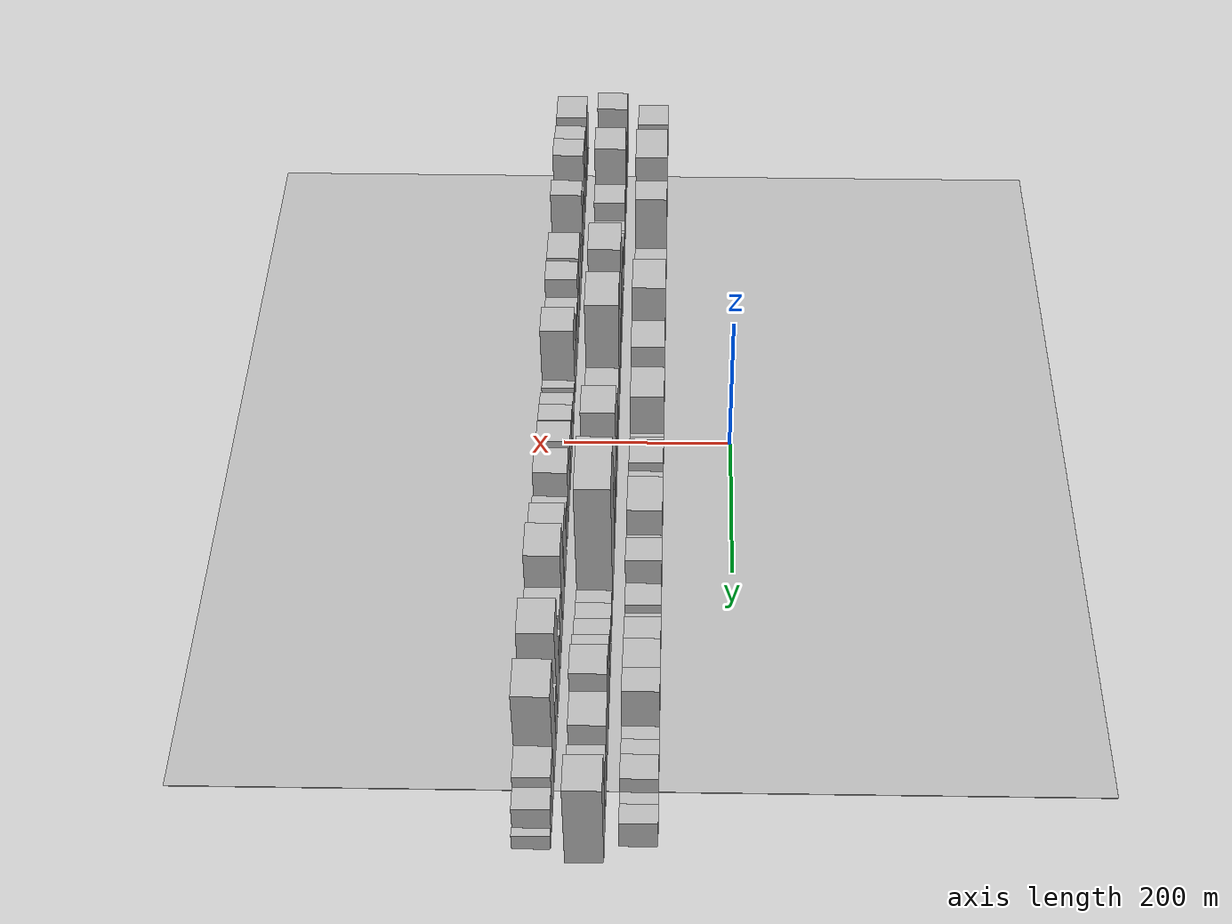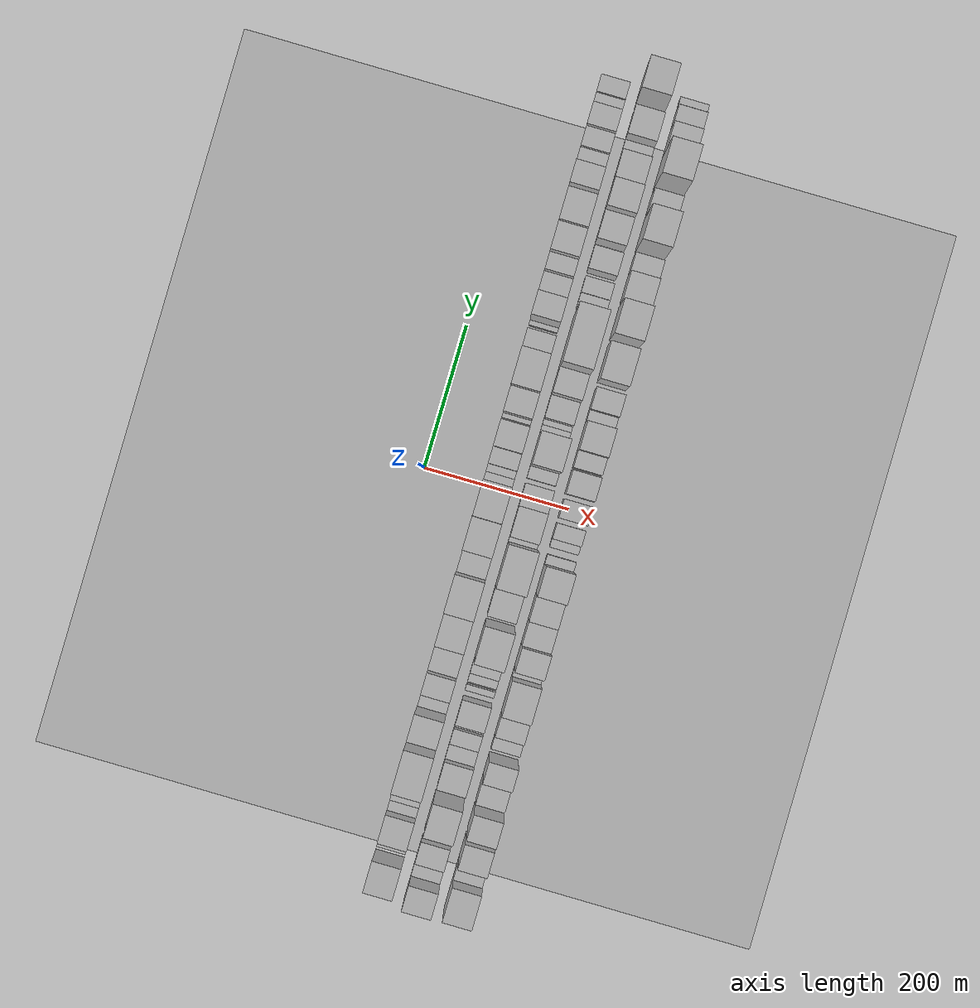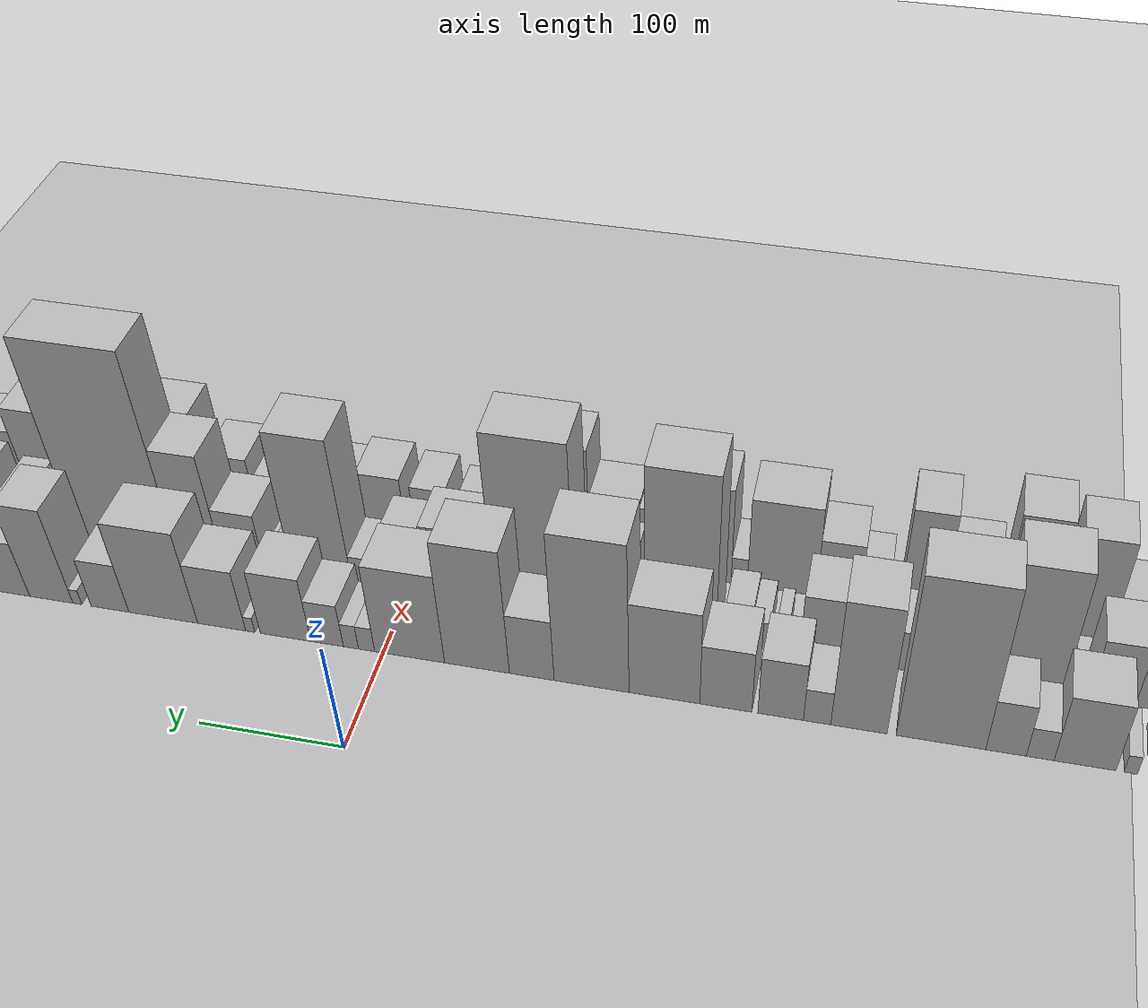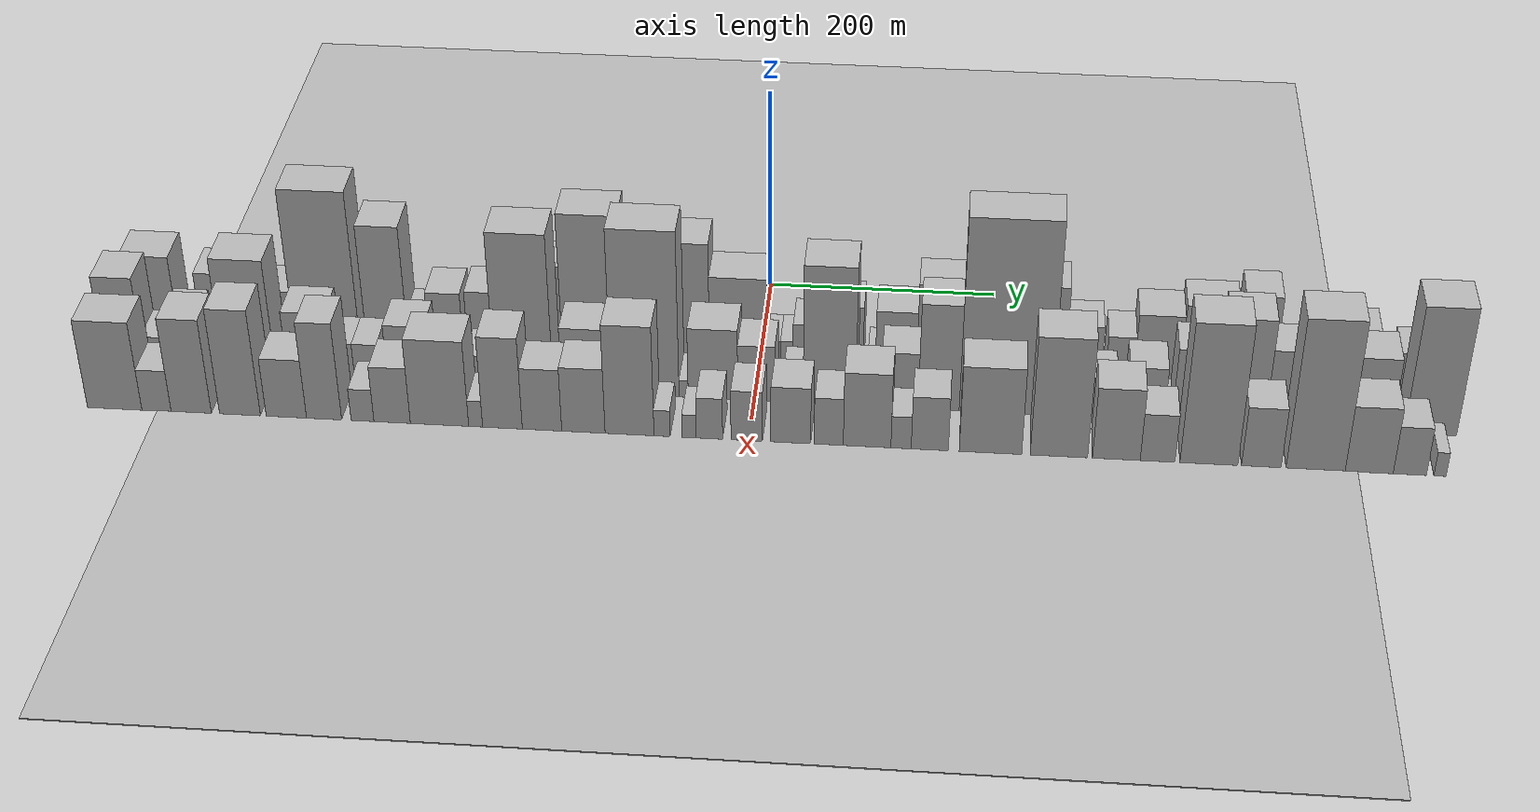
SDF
<?xml version="1.0" encoding="utf-8"?>

<sdf version="1.6">

   <world name="default">

      <gui fullscreen="0">

         <camera name="user_camera">

            <pose>-15 0 4.57585 0 0 0</pose>

            <view_controller>orbit</view_controller>

         </camera>

      </gui>

      <scene>

         <sky>

           <clouds>

             <speed>12</speed>

           </clouds>

         </sky>

         <ambient>0.4 0.4 0.4 1</ambient>

         <background>0.7 0.7 0.7 1</background>

         <shadows>1</shadows>

      </scene>

      <gravity>0 0 -9.8066</gravity>

      <magnetic_field>6e-06 2.3e-05 -4.2e-05</magnetic_field>

      <physics default="0" name="default_physics" type="ode">

         <ode>

            <solver>

               <type>quick</type>

               <iters>10</iters>

               <sor>1.0</sor>

               <use_dynamic_moi_rescaling>0</use_dynamic_moi_rescaling>

            </solver>

            <constraints>

               <cfm>0</cfm>

               <erp>0.2</erp>

               <contact_max_correcting_vel>100</contact_max_correcting_vel>

               <contact_surface_layer>0.001</contact_surface_layer>

            </constraints>

         </ode>

         <max_step_size>0.004</max_step_size>

         <real_time_factor>1</real_time_factor>

         <real_time_update_rate>250</real_time_update_rate>

      </physics>

      <light name="sun" type="directional">

         <cast_shadows>1</cast_shadows>

         <pose>0 0 10 0 0 0</pose>

         <diffuse>0.8 0.8 0.8 1</diffuse>

         <specular>0.2 0.2 0.2 1</specular>

         <attenuation>

            <range>1000</range>

            <constant>0.9</constant>

            <linear>0.01</linear>

            <quadratic>0.001</quadratic>

         </attenuation>

         <direction>-0.5 0.1 -0.9</direction>

      </light>

      <include>

         <name>ground_plane_1</name>

         <uri>model://HANNAS_ground_plane</uri>

         <pose>0 0 0  0 0 0</pose>

      </include>

      <include>

         <name>ground_plane_2</name>

         <uri>model://HANNAS_ground_plane</uri>

         <pose>100 0 0  0 0 0</pose>

      </include>

      <model name="building_1">

         <static>1</static>

         <pose frame="">100.0000 -532.4444 0 0.000000 0.000000 0.000000</pose>

         <link name="link">

            <pose frame="">0 0 40.50 0 0 0</pose>

            <collision name="collision">

               <geometry>

                  <box>

                     <size>40.0000 43.1112 81.0000</size>

                  </box>

               </geometry>

               <max_contacts>10</max_contacts>

               <surface>

                  <contact>

                     <ode/>

                  </contact>

                  <bounce/>

                  <friction>

                     <torsional>

                        <ode/>

                     </torsional>

                     <ode/>

                  </friction>

               </surface>

            </collision>

            <visual name="visual">

               <cast_shadows>0</cast_shadows>

               <geometry>

                  <box>

                     <size>40.0000 43.1112 81.0000</size>

                  </box>

               </geometry>

               <material>

                  <script>

                     <uri>model://HANNAS_wall/materials/scripts</uri>

                     <uri>model://HANNAS_wall/materials/textures</uri>

                     <name>vrc/HANNAS_wall</name>

                  </script>

               </material>

            </visual>

            <self_collide>0</self_collide>

            <enable_wind>0</enable_wind>

            <kinematic>0</kinematic>

         </link>

      </model>

      <model name="building_2">

         <static>1</static>

         <pose frame="">100.0000 -499.6300 0 0.000000 0.000000 0.000000</pose>

         <link name="link">

            <pose frame="">0 0 9.00 0 0 0</pose>

            <collision name="collision">

               <geometry>

                  <box>

                     <size>40.0000 8.5176 18.0000</size>

                  </box>

               </geometry>

               <max_contacts>10</max_contacts>

               <surface>

                  <contact>

                     <ode/>

                  </contact>

                  <bounce/>

                  <friction>

                     <torsional>

                        <ode/>

                     </torsional>

                     <ode/>

                  </friction>

               </surface>

            </collision>

            <visual name="visual">

               <cast_shadows>0</cast_shadows>

               <geometry>

                  <box>

                     <size>40.0000 8.5176 18.0000</size>

                  </box>

               </geometry>

               <material>

                  <script>

                     <uri>model://HANNAS_wall/materials/scripts</uri>

                     <uri>model://HANNAS_wall/materials/textures</uri>

                     <name>vrc/HANNAS_wall</name>

                  </script>

               </material>

            </visual>

            <self_collide>0</self_collide>

            <enable_wind>0</enable_wind>

            <kinematic>0</kinematic>

         </link>

      </model>

      <model name="building_3">

         <static>1</static>

         <pose frame="">100.0000 -470.8818 0 0.000000 0.000000 0.000000</pose>

         <link name="link">

            <pose frame="">0 0 33.00 0 0 0</pose>

            <collision name="collision">

               <geometry>

                  <box>

                     <size>40.0000 38.9788 66.0000</size>

                  </box>

               </geometry>

               <max_contacts>10</max_contacts>

               <surface>

                  <contact>

                     <ode/>

                  </contact>

                  <bounce/>

                  <friction>

                     <torsional>

                        <ode/>

                     </torsional>

                     <ode/>

                  </friction>

               </surface>

            </collision>

            <visual name="visual">

               <cast_shadows>0</cast_shadows>

               <geometry>

                  <box>

                     <size>40.0000 38.9788 66.0000</size>

                  </box>

               </geometry>

               <material>

                  <script>

                     <uri>model://HANNAS_wall/materials/scripts</uri>

                     <uri>model://HANNAS_wall/materials/textures</uri>

                     <name>vrc/HANNAS_wall</name>

                  </script>

               </material>

            </visual>

            <self_collide>0</self_collide>

            <enable_wind>0</enable_wind>

            <kinematic>0</kinematic>

         </link>

      </model>

      <model name="building_4">

         <static>1</static>

         <pose frame="">100.0000 -442.5654 0 0.000000 0.000000 0.000000</pose>

         <link name="link">

            <pose frame="">0 0 15.00 0 0 0</pose>

            <collision name="collision">

               <geometry>

                  <box>

                     <size>40.0000 17.6540 30.0000</size>

                  </box>

               </geometry>

               <max_contacts>10</max_contacts>

               <surface>

                  <contact>

                     <ode/>

                  </contact>

                  <bounce/>

                  <friction>

                     <torsional>

                        <ode/>

                     </torsional>

                     <ode/>

                  </friction>

               </surface>

            </collision>

            <visual name="visual">

               <cast_shadows>0</cast_shadows>

               <geometry>

                  <box>

                     <size>40.0000 17.6540 30.0000</size>

                  </box>

               </geometry>

               <material>

                  <script>

                     <uri>model://HANNAS_wall/materials/scripts</uri>

                     <uri>model://HANNAS_wall/materials/textures</uri>

                     <name>vrc/HANNAS_wall</name>

                  </script>

               </material>

            </visual>

            <self_collide>0</self_collide>

            <enable_wind>0</enable_wind>

            <kinematic>0</kinematic>

         </link>

      </model>

      <model name="building_5">

         <static>1</static>

         <pose frame="">100.0000 -420.7631 0 0.000000 0.000000 0.000000</pose>

         <link name="link">

            <pose frame="">0 0 25.50 0 0 0</pose>

            <collision name="collision">

               <geometry>

                  <box>

                     <size>40.0000 25.9506 51.0000</size>

                  </box>

               </geometry>

               <max_contacts>10</max_contacts>

               <surface>

                  <contact>

                     <ode/>

                  </contact>

                  <bounce/>

                  <friction>

                     <torsional>

                        <ode/>

                     </torsional>

                     <ode/>

                  </friction>

               </surface>

            </collision>

            <visual name="visual">

               <cast_shadows>0</cast_shadows>

               <geometry>

                  <box>

                     <size>40.0000 25.9506 51.0000</size>

                  </box>

               </geometry>

               <material>

                  <script>

                     <uri>model://HANNAS_wall/materials/scripts</uri>

                     <uri>model://HANNAS_wall/materials/textures</uri>

                     <name>vrc/HANNAS_wall</name>

                  </script>

               </material>

            </visual>

            <self_collide>0</self_collide>

            <enable_wind>0</enable_wind>

            <kinematic>0</kinematic>

         </link>

      </model>

      <model name="building_6">

         <static>1</static>

         <pose frame="">100.0000 -378.8792 0 0.000000 0.000000 0.000000</pose>

         <link name="link">

            <pose frame="">0 0 78.00 0 0 0</pose>

            <collision name="collision">

               <geometry>

                  <box>

                     <size>40.0000 57.8170 156.0000</size>

                  </box>

               </geometry>

               <max_contacts>10</max_contacts>

               <surface>

                  <contact>

                     <ode/>

                  </contact>

                  <bounce/>

                  <friction>

                     <torsional>

                        <ode/>

                     </torsional>

                     <ode/>

                  </friction>

               </surface>

            </collision>

            <visual name="visual">

               <cast_shadows>0</cast_shadows>

               <geometry>

                  <box>

                     <size>40.0000 57.8170 156.0000</size>

                  </box>

               </geometry>

               <material>

                  <script>

                     <uri>model://HANNAS_wall/materials/scripts</uri>

                     <uri>model://HANNAS_wall/materials/textures</uri>

                     <name>vrc/HANNAS_wall</name>

                  </script>

               </material>

            </visual>

            <self_collide>0</self_collide>

            <enable_wind>0</enable_wind>

            <kinematic>0</kinematic>

         </link>

      </model>

      <model name="building_7">

         <static>1</static>

         <pose frame="">100.0000 -325.5151 0 0.000000 0.000000 0.000000</pose>

         <link name="link">

            <pose frame="">0 0 61.50 0 0 0</pose>

            <collision name="collision">

               <geometry>

                  <box>

                     <size>40.0000 36.9112 123.0000</size>

                  </box>

               </geometry>

               <max_contacts>10</max_contacts>

               <surface>

                  <contact>

                     <ode/>

                  </contact>

                  <bounce/>

                  <friction>

                     <torsional>

                        <ode/>

                     </torsional>

                     <ode/>

                  </friction>

               </surface>

            </collision>

            <visual name="visual">

               <cast_shadows>0</cast_shadows>

               <geometry>

                  <box>

                     <size>40.0000 36.9112 123.0000</size>

                  </box>

               </geometry>

               <material>

                  <script>

                     <uri>model://HANNAS_wall/materials/scripts</uri>

                     <uri>model://HANNAS_wall/materials/textures</uri>

                     <name>vrc/HANNAS_wall</name>

                  </script>

               </material>

            </visual>

            <self_collide>0</self_collide>

            <enable_wind>0</enable_wind>

            <kinematic>0</kinematic>

         </link>

      </model>

      <model name="building_8">

         <static>1</static>

         <pose frame="">100.0000 -298.0300 0 0.000000 0.000000 0.000000</pose>

         <link name="link">

            <pose frame="">0 0 16.50 0 0 0</pose>

            <collision name="collision">

               <geometry>

                  <box>

                     <size>40.0000 18.0589 33.0000</size>

                  </box>

               </geometry>

               <max_contacts>10</max_contacts>

               <surface>

                  <contact>

                     <ode/>

                  </contact>

                  <bounce/>

                  <friction>

                     <torsional>

                        <ode/>

                     </torsional>

                     <ode/>

                  </friction>

               </surface>

            </collision>

            <visual name="visual">

               <cast_shadows>0</cast_shadows>

               <geometry>

                  <box>

                     <size>40.0000 18.0589 33.0000</size>

                  </box>

               </geometry>

               <material>

                  <script>

                     <uri>model://HANNAS_wall/materials/scripts</uri>

                     <uri>model://HANNAS_wall/materials/textures</uri>

                     <name>vrc/HANNAS_wall</name>

                  </script>

               </material>

            </visual>

            <self_collide>0</self_collide>

            <enable_wind>0</enable_wind>

            <kinematic>0</kinematic>

         </link>

      </model>

      <model name="building_9">

         <static>1</static>

         <pose frame="">100.0000 -273.8442 0 0.000000 0.000000 0.000000</pose>

         <link name="link">

            <pose frame="">0 0 28.50 0 0 0</pose>

            <collision name="collision">

               <geometry>

                  <box>

                     <size>40.0000 30.3128 57.0000</size>

                  </box>

               </geometry>

               <max_contacts>10</max_contacts>

               <surface>

                  <contact>

                     <ode/>

                  </contact>

                  <bounce/>

                  <friction>

                     <torsional>

                        <ode/>

                     </torsional>

                     <ode/>

                  </friction>

               </surface>

            </collision>

            <visual name="visual">

               <cast_shadows>0</cast_shadows>

               <geometry>

                  <box>

                     <size>40.0000 30.3128 57.0000</size>

                  </box>

               </geometry>

               <material>

                  <script>

                     <uri>model://HANNAS_wall/materials/scripts</uri>

                     <uri>model://HANNAS_wall/materials/textures</uri>

                     <name>vrc/HANNAS_wall</name>

                  </script>

               </material>

            </visual>

            <self_collide>0</self_collide>

            <enable_wind>0</enable_wind>

            <kinematic>0</kinematic>

         </link>

      </model>

      <model name="building_10">

         <static>1</static>

         <pose frame="">100.0000 -237.2336 0 0.000000 0.000000 0.000000</pose>

         <link name="link">

            <pose frame="">0 0 30.00 0 0 0</pose>

            <collision name="collision">

               <geometry>

                  <box>

                     <size>40.0000 34.9083 60.0000</size>

                  </box>

               </geometry>

               <max_contacts>10</max_contacts>

               <surface>

                  <contact>

                     <ode/>

                  </contact>

                  <bounce/>

                  <friction>

                     <torsional>

                        <ode/>

                     </torsional>

                     <ode/>

                  </friction>

               </surface>

            </collision>

            <visual name="visual">

               <cast_shadows>0</cast_shadows>

               <geometry>

                  <box>

                     <size>40.0000 34.9083 60.0000</size>

                  </box>

               </geometry>

               <material>

                  <script>

                     <uri>model://HANNAS_wall/materials/scripts</uri>

                     <uri>model://HANNAS_wall/materials/textures</uri>

                     <name>vrc/HANNAS_wall</name>

                  </script>

               </material>

            </visual>

            <self_collide>0</self_collide>

            <enable_wind>0</enable_wind>

            <kinematic>0</kinematic>

         </link>

      </model>

      <model name="building_11">

         <static>1</static>

         <pose frame="">100.0000 -195.7393 0 0.000000 0.000000 0.000000</pose>

         <link name="link">

            <pose frame="">0 0 45.00 0 0 0</pose>

            <collision name="collision">

               <geometry>

                  <box>

                     <size>40.0000 48.0804 90.0000</size>

                  </box>

               </geometry>

               <max_contacts>10</max_contacts>

               <surface>

                  <contact>

                     <ode/>

                  </contact>

                  <bounce/>

                  <friction>

                     <torsional>

                        <ode/>

                     </torsional>

                     <ode/>

                  </friction>

               </surface>

            </collision>

            <visual name="visual">

               <cast_shadows>0</cast_shadows>

               <geometry>

                  <box>

                     <size>40.0000 48.0804 90.0000</size>

                  </box>

               </geometry>

               <material>

                  <script>

                     <uri>model://HANNAS_wall/materials/scripts</uri>

                     <uri>model://HANNAS_wall/materials/textures</uri>

                     <name>vrc/HANNAS_wall</name>

                  </script>

               </material>

            </visual>

            <self_collide>0</self_collide>

            <enable_wind>0</enable_wind>

            <kinematic>0</kinematic>

         </link>

      </model>

      <model name="building_12">

         <static>1</static>

         <pose frame="">100.0000 -145.9250 0 0.000000 0.000000 0.000000</pose>

         <link name="link">

            <pose frame="">0 0 72.00 0 0 0</pose>

            <collision name="collision">

               <geometry>

                  <box>

                     <size>40.0000 51.5482 144.0000</size>

                  </box>

               </geometry>

               <max_contacts>10</max_contacts>

               <surface>

                  <contact>

                     <ode/>

                  </contact>

                  <bounce/>

                  <friction>

                     <torsional>

                        <ode/>

                     </torsional>

                     <ode/>

                  </friction>

               </surface>

            </collision>

            <visual name="visual">

               <cast_shadows>0</cast_shadows>

               <geometry>

                  <box>

                     <size>40.0000 51.5482 144.0000</size>

                  </box>

               </geometry>

               <material>

                  <script>

                     <uri>model://HANNAS_wall/materials/scripts</uri>

                     <uri>model://HANNAS_wall/materials/textures</uri>

                     <name>vrc/HANNAS_wall</name>

                  </script>

               </material>

            </visual>

            <self_collide>0</self_collide>

            <enable_wind>0</enable_wind>

            <kinematic>0</kinematic>

         </link>

      </model>

      <model name="building_13">

         <static>1</static>

         <pose frame="">100.0000 -104.5609 0 0.000000 0.000000 0.000000</pose>

         <link name="link">

            <pose frame="">0 0 30.00 0 0 0</pose>

            <collision name="collision">

               <geometry>

                  <box>

                     <size>40.0000 31.1801 60.0000</size>

                  </box>

               </geometry>

               <max_contacts>10</max_contacts>

               <surface>

                  <contact>

                     <ode/>

                  </contact>

                  <bounce/>

                  <friction>

                     <torsional>

                        <ode/>

                     </torsional>

                     <ode/>

                  </friction>

               </surface>

            </collision>

            <visual name="visual">

               <cast_shadows>0</cast_shadows>

               <geometry>

                  <box>

                     <size>40.0000 31.1801 60.0000</size>

                  </box>

               </geometry>

               <material>

                  <script>

                     <uri>model://HANNAS_wall/materials/scripts</uri>

                     <uri>model://HANNAS_wall/materials/textures</uri>

                     <name>vrc/HANNAS_wall</name>

                  </script>

               </material>

            </visual>

            <self_collide>0</self_collide>

            <enable_wind>0</enable_wind>

            <kinematic>0</kinematic>

         </link>

      </model>

      <model name="building_14">

         <static>1</static>

         <pose frame="">100.0000 -66.1938 0 0.000000 0.000000 0.000000</pose>

         <link name="link">

            <pose frame="">0 0 60.00 0 0 0</pose>

            <collision name="collision">

               <geometry>

                  <box>

                     <size>40.0000 45.5540 120.0000</size>

                  </box>

               </geometry>

               <max_contacts>10</max_contacts>

               <surface>

                  <contact>

                     <ode/>

                  </contact>

                  <bounce/>

                  <friction>

                     <torsional>

                        <ode/>

                     </torsional>

                     <ode/>

                  </friction>

               </surface>

            </collision>

            <visual name="visual">

               <cast_shadows>0</cast_shadows>

               <geometry>

                  <box>

                     <size>40.0000 45.5540 120.0000</size>

                  </box>

               </geometry>

               <material>

                  <script>

                     <uri>model://HANNAS_wall/materials/scripts</uri>

                     <uri>model://HANNAS_wall/materials/textures</uri>

                     <name>vrc/HANNAS_wall</name>

                  </script>

               </material>

            </visual>

            <self_collide>0</self_collide>

            <enable_wind>0</enable_wind>

            <kinematic>0</kinematic>

         </link>

      </model>

      <model name="building_15">

         <static>1</static>

         <pose frame="">100.0000 -18.5358 0 0.000000 0.000000 0.000000</pose>

         <link name="link">

            <pose frame="">0 0 43.50 0 0 0</pose>

            <collision name="collision">

               <geometry>

                  <box>

                     <size>40.0000 49.7620 87.0000</size>

                  </box>

               </geometry>

               <max_contacts>10</max_contacts>

               <surface>

                  <contact>

                     <ode/>

                  </contact>

                  <bounce/>

                  <friction>

                     <torsional>

                        <ode/>

                     </torsional>

                     <ode/>

                  </friction>

               </surface>

            </collision>

            <visual name="visual">

               <cast_shadows>0</cast_shadows>

               <geometry>

                  <box>

                     <size>40.0000 49.7620 87.0000</size>

                  </box>

               </geometry>

               <material>

                  <script>

                     <uri>model://HANNAS_wall/materials/scripts</uri>

                     <uri>model://HANNAS_wall/materials/textures</uri>

                     <name>vrc/HANNAS_wall</name>

                  </script>

               </material>

            </visual>

            <self_collide>0</self_collide>

            <enable_wind>0</enable_wind>

            <kinematic>0</kinematic>

         </link>

      </model>

      <model name="building_16">

         <static>1</static>

         <pose frame="">100.0000 12.1694 0 0.000000 0.000000 0.000000</pose>

         <link name="link">

            <pose frame="">0 0 12.00 0 0 0</pose>

            <collision name="collision">

               <geometry>

                  <box>

                     <size>40.0000 11.6483 24.0000</size>

                  </box>

               </geometry>

               <max_contacts>10</max_contacts>

               <surface>

                  <contact>

                     <ode/>

                  </contact>

                  <bounce/>

                  <friction>

                     <torsional>

                        <ode/>

                     </torsional>

                     <ode/>

                  </friction>

               </surface>

            </collision>

            <visual name="visual">

               <cast_shadows>0</cast_shadows>

               <geometry>

                  <box>

                     <size>40.0000 11.6483 24.0000</size>

                  </box>

               </geometry>

               <material>

                  <script>

                     <uri>model://HANNAS_wall/materials/scripts</uri>

                     <uri>model://HANNAS_wall/materials/textures</uri>

                     <name>vrc/HANNAS_wall</name>

                  </script>

               </material>

            </visual>

            <self_collide>0</self_collide>

            <enable_wind>0</enable_wind>

            <kinematic>0</kinematic>

         </link>

      </model>

      <model name="building_17">

         <static>1</static>

         <pose frame="">100.0000 23.4495 0 0.000000 0.000000 0.000000</pose>

         <link name="link">

            <pose frame="">0 0 12.00 0 0 0</pose>

            <collision name="collision">

               <geometry>

                  <box>

                     <size>40.0000 10.9120 24.0000</size>

                  </box>

               </geometry>

               <max_contacts>10</max_contacts>

               <surface>

                  <contact>

                     <ode/>

                  </contact>

                  <bounce/>

                  <friction>

                     <torsional>

                        <ode/>

                     </torsional>

                     <ode/>

                  </friction>

               </surface>

            </collision>

            <visual name="visual">

               <cast_shadows>0</cast_shadows>

               <geometry>

                  <box>

                     <size>40.0000 10.9120 24.0000</size>

                  </box>

               </geometry>

               <material>

                  <script>

                     <uri>model://HANNAS_wall/materials/scripts</uri>

                     <uri>model://HANNAS_wall/materials/textures</uri>

                     <name>vrc/HANNAS_wall</name>

                  </script>

               </material>

            </visual>

            <self_collide>0</self_collide>

            <enable_wind>0</enable_wind>

            <kinematic>0</kinematic>

         </link>

      </model>

      <model name="building_18">

         <static>1</static>

         <pose frame="">100.0000 40.6644 0 0.000000 0.000000 0.000000</pose>

         <link name="link">

            <pose frame="">0 0 21.00 0 0 0</pose>

            <collision name="collision">

               <geometry>

                  <box>

                     <size>40.0000 23.5177 42.0000</size>

                  </box>

               </geometry>

               <max_contacts>10</max_contacts>

               <surface>

                  <contact>

                     <ode/>

                  </contact>

                  <bounce/>

                  <friction>

                     <torsional>

                        <ode/>

                     </torsional>

                     <ode/>

                  </friction>

               </surface>

            </collision>

            <visual name="visual">

               <cast_shadows>0</cast_shadows>

               <geometry>

                  <box>

                     <size>40.0000 23.5177 42.0000</size>

                  </box>

               </geometry>

               <material>

                  <script>

                     <uri>model://HANNAS_wall/materials/scripts</uri>

                     <uri>model://HANNAS_wall/materials/textures</uri>

                     <name>vrc/HANNAS_wall</name>

                  </script>

               </material>

            </visual>

            <self_collide>0</self_collide>

            <enable_wind>0</enable_wind>

            <kinematic>0</kinematic>

         </link>

      </model>

      <model name="building_19">

         <static>1</static>

         <pose frame="">100.0000 70.8931 0 0.000000 0.000000 0.000000</pose>

         <link name="link">

            <pose frame="">0 0 31.50 0 0 0</pose>

            <collision name="collision">

               <geometry>

                  <box>

                     <size>40.0000 36.9398 63.0000</size>

                  </box>

               </geometry>

               <max_contacts>10</max_contacts>

               <surface>

                  <contact>

                     <ode/>

                  </contact>

                  <bounce/>

                  <friction>

                     <torsional>

                        <ode/>

                     </torsional>

                     <ode/>

                  </friction>

               </surface>

            </collision>

            <visual name="visual">

               <cast_shadows>0</cast_shadows>

               <geometry>

                  <box>

                     <size>40.0000 36.9398 63.0000</size>

                  </box>

               </geometry>

               <material>

                  <script>

                     <uri>model://HANNAS_wall/materials/scripts</uri>

                     <uri>model://HANNAS_wall/materials/textures</uri>

                     <name>vrc/HANNAS_wall</name>

                  </script>

               </material>

            </visual>

            <self_collide>0</self_collide>

            <enable_wind>0</enable_wind>

            <kinematic>0</kinematic>

         </link>

      </model>

      <model name="building_20">

         <static>1</static>

         <pose frame="">100.0000 96.7150 0 0.000000 0.000000 0.000000</pose>

         <link name="link">

            <pose frame="">0 0 7.50 0 0 0</pose>

            <collision name="collision">

               <geometry>

                  <box>

                     <size>40.0000 6.7040 15.0000</size>

                  </box>

               </geometry>

               <max_contacts>10</max_contacts>

               <surface>

                  <contact>

                     <ode/>

                  </contact>

                  <bounce/>

                  <friction>

                     <torsional>

                        <ode/>

                     </torsional>

                     <ode/>

                  </friction>

               </surface>

            </collision>

            <visual name="visual">

               <cast_shadows>0</cast_shadows>

               <geometry>

                  <box>

                     <size>40.0000 6.7040 15.0000</size>

                  </box>

               </geometry>

               <material>

                  <script>

                     <uri>model://HANNAS_wall/materials/scripts</uri>

                     <uri>model://HANNAS_wall/materials/textures</uri>

                     <name>vrc/HANNAS_wall</name>

                  </script>

               </material>

            </visual>

            <self_collide>0</self_collide>

            <enable_wind>0</enable_wind>

            <kinematic>0</kinematic>

         </link>

      </model>

      <model name="building_21">

         <static>1</static>

         <pose frame="">100.0000 117.7842 0 0.000000 0.000000 0.000000</pose>

         <link name="link">

            <pose frame="">0 0 30.00 0 0 0</pose>

            <collision name="collision">

               <geometry>

                  <box>

                     <size>40.0000 35.4345 60.0000</size>

                  </box>

               </geometry>

               <max_contacts>10</max_contacts>

               <surface>

                  <contact>

                     <ode/>

                  </contact>

                  <bounce/>

                  <friction>

                     <torsional>

                        <ode/>

                     </torsional>

                     <ode/>

                  </friction>

               </surface>

            </collision>

            <visual name="visual">

               <cast_shadows>0</cast_shadows>

               <geometry>

                  <box>

                     <size>40.0000 35.4345 60.0000</size>

                  </box>

               </geometry>

               <material>

                  <script>

                     <uri>model://HANNAS_wall/materials/scripts</uri>

                     <uri>model://HANNAS_wall/materials/textures</uri>

                     <name>vrc/HANNAS_wall</name>

                  </script>

               </material>

            </visual>

            <self_collide>0</self_collide>

            <enable_wind>0</enable_wind>

            <kinematic>0</kinematic>

         </link>

      </model>

      <model name="building_22">

         <static>1</static>

         <pose frame="">100.0000 161.2391 0 0.000000 0.000000 0.000000</pose>

         <link name="link">

            <pose frame="">0 0 45.00 0 0 0</pose>

            <collision name="collision">

               <geometry>

                  <box>

                     <size>40.0000 51.4753 90.0000</size>

                  </box>

               </geometry>

               <max_contacts>10</max_contacts>

               <surface>

                  <contact>

                     <ode/>

                  </contact>

                  <bounce/>

                  <friction>

                     <torsional>

                        <ode/>

                     </torsional>

                     <ode/>

                  </friction>

               </surface>

            </collision>

            <visual name="visual">

               <cast_shadows>0</cast_shadows>

               <geometry>

                  <box>

                     <size>40.0000 51.4753 90.0000</size>

                  </box>

               </geometry>

               <material>

                  <script>

                     <uri>model://HANNAS_wall/materials/scripts</uri>

                     <uri>model://HANNAS_wall/materials/textures</uri>

                     <name>vrc/HANNAS_wall</name>

                  </script>

               </material>

            </visual>

            <self_collide>0</self_collide>

            <enable_wind>0</enable_wind>

            <kinematic>0</kinematic>

         </link>

      </model>

      <model name="building_23">

         <static>1</static>

         <pose frame="">100.0000 201.2230 0 0.000000 0.000000 0.000000</pose>

         <link name="link">

            <pose frame="">0 0 24.00 0 0 0</pose>

            <collision name="collision">

               <geometry>

                  <box>

                     <size>40.0000 28.4923 48.0000</size>

                  </box>

               </geometry>

               <max_contacts>10</max_contacts>

               <surface>

                  <contact>

                     <ode/>

                  </contact>

                  <bounce/>

                  <friction>

                     <torsional>

                        <ode/>

                     </torsional>

                     <ode/>

                  </friction>

               </surface>

            </collision>

            <visual name="visual">

               <cast_shadows>0</cast_shadows>

               <geometry>

                  <box>

                     <size>40.0000 28.4923 48.0000</size>

                  </box>

               </geometry>

               <material>

                  <script>

                     <uri>model://HANNAS_wall/materials/scripts</uri>

                     <uri>model://HANNAS_wall/materials/textures</uri>

                     <name>vrc/HANNAS_wall</name>

                  </script>

               </material>

            </visual>

            <self_collide>0</self_collide>

            <enable_wind>0</enable_wind>

            <kinematic>0</kinematic>

         </link>

      </model>

      <model name="building_24">

         <static>1</static>

         <pose frame="">100.0000 225.8914 0 0.000000 0.000000 0.000000</pose>

         <link name="link">

            <pose frame="">0 0 7.50 0 0 0</pose>

            <collision name="collision">

               <geometry>

                  <box>

                     <size>40.0000 6.8446 15.0000</size>

                  </box>

               </geometry>

               <max_contacts>10</max_contacts>

               <surface>

                  <contact>

                     <ode/>

                  </contact>

                  <bounce/>

                  <friction>

                     <torsional>

                        <ode/>

                     </torsional>

                     <ode/>

                  </friction>

               </surface>

            </collision>

            <visual name="visual">

               <cast_shadows>0</cast_shadows>

               <geometry>

                  <box>

                     <size>40.0000 6.8446 15.0000</size>

                  </box>

               </geometry>

               <material>

                  <script>

                     <uri>model://HANNAS_wall/materials/scripts</uri>

                     <uri>model://HANNAS_wall/materials/textures</uri>

                     <name>vrc/HANNAS_wall</name>

                  </script>

               </material>

            </visual>

            <self_collide>0</self_collide>

            <enable_wind>0</enable_wind>

            <kinematic>0</kinematic>

         </link>

      </model>

      <model name="building_25">

         <static>1</static>

         <pose frame="">100.0000 245.7878 0 0.000000 0.000000 0.000000</pose>

         <link name="link">

            <pose frame="">0 0 46.50 0 0 0</pose>

            <collision name="collision">

               <geometry>

                  <box>

                     <size>40.0000 32.9482 93.0000</size>

                  </box>

               </geometry>

               <max_contacts>10</max_contacts>

               <surface>

                  <contact>

                     <ode/>

                  </contact>

                  <bounce/>

                  <friction>

                     <torsional>

                        <ode/>

                     </torsional>

                     <ode/>

                  </friction>

               </surface>

            </collision>

            <visual name="visual">

               <cast_shadows>0</cast_shadows>

               <geometry>

                  <box>

                     <size>40.0000 32.9482 93.0000</size>

                  </box>

               </geometry>

               <material>

                  <script>

                     <uri>model://HANNAS_wall/materials/scripts</uri>

                     <uri>model://HANNAS_wall/materials/textures</uri>

                     <name>vrc/HANNAS_wall</name>

                  </script>

               </material>

            </visual>

            <self_collide>0</self_collide>

            <enable_wind>0</enable_wind>

            <kinematic>0</kinematic>

         </link>

      </model>

      <model name="building_26">

         <static>1</static>

         <pose frame="">100.0000 277.6288 0 0.000000 0.000000 0.000000</pose>

         <link name="link">

            <pose frame="">0 0 27.00 0 0 0</pose>

            <collision name="collision">

               <geometry>

                  <box>

                     <size>40.0000 30.7338 54.0000</size>

                  </box>

               </geometry>

               <max_contacts>10</max_contacts>

               <surface>

                  <contact>

                     <ode/>

                  </contact>

                  <bounce/>

                  <friction>

                     <torsional>

                        <ode/>

                     </torsional>

                     <ode/>

                  </friction>

               </surface>

            </collision>

            <visual name="visual">

               <cast_shadows>0</cast_shadows>

               <geometry>

                  <box>

                     <size>40.0000 30.7338 54.0000</size>

                  </box>

               </geometry>

               <material>

                  <script>

                     <uri>model://HANNAS_wall/materials/scripts</uri>

                     <uri>model://HANNAS_wall/materials/textures</uri>

                     <name>vrc/HANNAS_wall</name>

                  </script>

               </material>

            </visual>

            <self_collide>0</self_collide>

            <enable_wind>0</enable_wind>

            <kinematic>0</kinematic>

         </link>

      </model>

      <model name="building_27">

         <static>1</static>

         <pose frame="">100.0000 308.9507 0 0.000000 0.000000 0.000000</pose>

         <link name="link">

            <pose frame="">0 0 22.50 0 0 0</pose>

            <collision name="collision">

               <geometry>

                  <box>

                     <size>40.0000 23.9101 45.0000</size>

                  </box>

               </geometry>

               <max_contacts>10</max_contacts>

               <surface>

                  <contact>

                     <ode/>

                  </contact>

                  <bounce/>

                  <friction>

                     <torsional>

                        <ode/>

                     </torsional>

                     <ode/>

                  </friction>

               </surface>

            </collision>

            <visual name="visual">

               <cast_shadows>0</cast_shadows>

               <geometry>

                  <box>

                     <size>40.0000 23.9101 45.0000</size>

                  </box>

               </geometry>

               <material>

                  <script>

                     <uri>model://HANNAS_wall/materials/scripts</uri>

                     <uri>model://HANNAS_wall/materials/textures</uri>

                     <name>vrc/HANNAS_wall</name>

                  </script>

               </material>

            </visual>

            <self_collide>0</self_collide>

            <enable_wind>0</enable_wind>

            <kinematic>0</kinematic>

         </link>

      </model>

      <model name="building_28">

         <static>1</static>

         <pose frame="">100.0000 340.4748 0 0.000000 0.000000 0.000000</pose>

         <link name="link">

            <pose frame="">0 0 34.50 0 0 0</pose>

            <collision name="collision">

               <geometry>

                  <box>

                     <size>40.0000 39.1380 69.0000</size>

                  </box>

               </geometry>

               <max_contacts>10</max_contacts>

               <surface>

                  <contact>

                     <ode/>

                  </contact>

                  <bounce/>

                  <friction>

                     <torsional>

                        <ode/>

                     </torsional>

                     <ode/>

                  </friction>

               </surface>

            </collision>

            <visual name="visual">

               <cast_shadows>0</cast_shadows>

               <geometry>

                  <box>

                     <size>40.0000 39.1380 69.0000</size>

                  </box>

               </geometry>

               <material>

                  <script>

                     <uri>model://HANNAS_wall/materials/scripts</uri>

                     <uri>model://HANNAS_wall/materials/textures</uri>

                     <name>vrc/HANNAS_wall</name>

                  </script>

               </material>

            </visual>

            <self_collide>0</self_collide>

            <enable_wind>0</enable_wind>

            <kinematic>0</kinematic>

         </link>

      </model>

      <model name="building_29">

         <static>1</static>

         <pose frame="">100.0000 382.3698 0 0.000000 0.000000 0.000000</pose>

         <link name="link">

            <pose frame="">0 0 40.50 0 0 0</pose>

            <collision name="collision">

               <geometry>

                  <box>

                     <size>40.0000 44.6520 81.0000</size>

                  </box>

               </geometry>

               <max_contacts>10</max_contacts>

               <surface>

                  <contact>

                     <ode/>

                  </contact>

                  <bounce/>

                  <friction>

                     <torsional>

                        <ode/>

                     </torsional>

                     <ode/>

                  </friction>

               </surface>

            </collision>

            <visual name="visual">

               <cast_shadows>0</cast_shadows>

               <geometry>

                  <box>

                     <size>40.0000 44.6520 81.0000</size>

                  </box>

               </geometry>

               <material>

                  <script>

                     <uri>model://HANNAS_wall/materials/scripts</uri>

                     <uri>model://HANNAS_wall/materials/textures</uri>

                     <name>vrc/HANNAS_wall</name>

                  </script>

               </material>

            </visual>

            <self_collide>0</self_collide>

            <enable_wind>0</enable_wind>

            <kinematic>0</kinematic>

         </link>

      </model>

      <model name="building_30">

         <static>1</static>

         <pose frame="">100.0000 423.3822 0 0.000000 0.000000 0.000000</pose>

         <link name="link">

            <pose frame="">0 0 46.50 0 0 0</pose>

            <collision name="collision">

               <geometry>

                  <box>

                     <size>40.0000 31.3728 93.0000</size>

                  </box>

               </geometry>

               <max_contacts>10</max_contacts>

               <surface>

                  <contact>

                     <ode/>

                  </contact>

                  <bounce/>

                  <friction>

                     <torsional>

                        <ode/>

                     </torsional>

                     <ode/>

                  </friction>

               </surface>

            </collision>

            <visual name="visual">

               <cast_shadows>0</cast_shadows>

               <geometry>

                  <box>

                     <size>40.0000 31.3728 93.0000</size>

                  </box>

               </geometry>

               <material>

                  <script>

                     <uri>model://HANNAS_wall/materials/scripts</uri>

                     <uri>model://HANNAS_wall/materials/textures</uri>

                     <name>vrc/HANNAS_wall</name>

                  </script>

               </material>

            </visual>

            <self_collide>0</self_collide>

            <enable_wind>0</enable_wind>

            <kinematic>0</kinematic>

         </link>

      </model>

      <model name="building_31">

         <static>1</static>

         <pose frame="">100.0000 455.3602 0 0.000000 0.000000 0.000000</pose>

         <link name="link">

            <pose frame="">0 0 19.50 0 0 0</pose>

            <collision name="collision">

               <geometry>

                  <box>

                     <size>40.0000 22.5831 39.0000</size>

                  </box>

               </geometry>

               <max_contacts>10</max_contacts>

               <surface>

                  <contact>

                     <ode/>

                  </contact>

                  <bounce/>

                  <friction>

                     <torsional>

                        <ode/>

                     </torsional>

                     <ode/>

                  </friction>

               </surface>

            </collision>

            <visual name="visual">

               <cast_shadows>0</cast_shadows>

               <geometry>

                  <box>

                     <size>40.0000 22.5831 39.0000</size>

                  </box>

               </geometry>

               <material>

                  <script>

                     <uri>model://HANNAS_wall/materials/scripts</uri>

                     <uri>model://HANNAS_wall/materials/textures</uri>

                     <name>vrc/HANNAS_wall</name>

                  </script>

               </material>

            </visual>

            <self_collide>0</self_collide>

            <enable_wind>0</enable_wind>

            <kinematic>0</kinematic>

         </link>

      </model>

      <model name="building_32">

         <static>1</static>

         <pose frame="">100.0000 480.3350 0 0.000000 0.000000 0.000000</pose>

         <link name="link">

            <pose frame="">0 0 24.00 0 0 0</pose>

            <collision name="collision">

               <geometry>

                  <box>

                     <size>40.0000 27.3665 48.0000</size>

                  </box>

               </geometry>

               <max_contacts>10</max_contacts>

               <surface>

                  <contact>

                     <ode/>

                  </contact>

                  <bounce/>

                  <friction>

                     <torsional>

                        <ode/>

                     </torsional>

                     <ode/>

                  </friction>

               </surface>

            </collision>

            <visual name="visual">

               <cast_shadows>0</cast_shadows>

               <geometry>

                  <box>

                     <size>40.0000 27.3665 48.0000</size>

                  </box>

               </geometry>

               <material>

                  <script>

                     <uri>model://HANNAS_wall/materials/scripts</uri>

                     <uri>model://HANNAS_wall/materials/textures</uri>

                     <name>vrc/HANNAS_wall</name>

                  </script>

               </material>

            </visual>

            <self_collide>0</self_collide>

            <enable_wind>0</enable_wind>

            <kinematic>0</kinematic>

         </link>

      </model>

      <model name="building_33">

         <static>1</static>

         <pose frame="">100.0000 509.3112 0 0.000000 0.000000 0.000000</pose>

         <link name="link">

            <pose frame="">0 0 30.00 0 0 0</pose>

            <collision name="collision">

               <geometry>

                  <box>

                     <size>40.0000 30.5859 60.0000</size>

                  </box>

               </geometry>

               <max_contacts>10</max_contacts>

               <surface>

                  <contact>

                     <ode/>

                  </contact>

                  <bounce/>

                  <friction>

                     <torsional>

                        <ode/>

                     </torsional>

                     <ode/>

                  </friction>

               </surface>

            </collision>

            <visual name="visual">

               <cast_shadows>0</cast_shadows>

               <geometry>

                  <box>

                     <size>40.0000 30.5859 60.0000</size>

                  </box>

               </geometry>

               <material>

                  <script>

                     <uri>model://HANNAS_wall/materials/scripts</uri>

                     <uri>model://HANNAS_wall/materials/textures</uri>

                     <name>vrc/HANNAS_wall</name>

                  </script>

               </material>

            </visual>

            <self_collide>0</self_collide>

            <enable_wind>0</enable_wind>

            <kinematic>0</kinematic>

         </link>

      </model>

      <model name="building_34">

         <static>1</static>

         <pose frame="">100.0000 533.6511 0 0.000000 0.000000 0.000000</pose>

         <link name="link">

            <pose frame="">0 0 18.00 0 0 0</pose>

            <collision name="collision">

               <geometry>

                  <box>

                     <size>40.0000 18.0937 36.0000</size>

                  </box>

               </geometry>

               <max_contacts>10</max_contacts>

               <surface>

                  <contact>

                     <ode/>

                  </contact>

                  <bounce/>

                  <friction>

                     <torsional>

                        <ode/>

                     </torsional>

                     <ode/>

                  </friction>

               </surface>

            </collision>

            <visual name="visual">

               <cast_shadows>0</cast_shadows>

               <geometry>

                  <box>

                     <size>40.0000 18.0937 36.0000</size>

                  </box>

               </geometry>

               <material>

                  <script>

                     <uri>model://HANNAS_wall/materials/scripts</uri>

                     <uri>model://HANNAS_wall/materials/textures</uri>

                     <name>vrc/HANNAS_wall</name>

                  </script>

               </material>

            </visual>

            <self_collide>0</self_collide>

            <enable_wind>0</enable_wind>

            <kinematic>0</kinematic>

         </link>

      </model>

      <model name="building_35">

         <static>1</static>

         <pose frame="">100.0000 554.5918 0 0.000000 0.000000 0.000000</pose>

         <link name="link">

            <pose frame="">0 0 21.00 0 0 0</pose>

            <collision name="collision">

               <geometry>

                  <box>

                     <size>40.0000 23.7879 42.0000</size>

                  </box>

               </geometry>

               <max_contacts>10</max_contacts>

               <surface>

                  <contact>

                     <ode/>

                  </contact>

                  <bounce/>

                  <friction>

                     <torsional>

                        <ode/>

                     </torsional>

                     <ode/>

                  </friction>

               </surface>

            </collision>

            <visual name="visual">

               <cast_shadows>0</cast_shadows>

               <geometry>

                  <box>

                     <size>40.0000 23.7879 42.0000</size>

                  </box>

               </geometry>

               <material>

                  <script>

                     <uri>model://HANNAS_wall/materials/scripts</uri>

                     <uri>model://HANNAS_wall/materials/textures</uri>

                     <name>vrc/HANNAS_wall</name>

                  </script>

               </material>

            </visual>

            <self_collide>0</self_collide>

            <enable_wind>0</enable_wind>

            <kinematic>0</kinematic>

         </link>

      </model>

      <model name="building_36">

         <static>1</static>

         <pose frame="">155.0000 -542.4896 0 0.000000 0.000000 0.000000</pose>

         <link name="link">

            <pose frame="">0 0 48.00 0 0 0</pose>

            <collision name="collision">

               <geometry>

                  <box>

                     <size>40.0000 35.0207 96.0000</size>

                  </box>

               </geometry>

               <max_contacts>10</max_contacts>

               <surface>

                  <contact>

                     <ode/>

                  </contact>

                  <bounce/>

                  <friction>

                     <torsional>

                        <ode/>

                     </torsional>

                     <ode/>

                  </friction>

               </surface>

            </collision>

            <visual name="visual">

               <cast_shadows>0</cast_shadows>

               <geometry>

                  <box>

                     <size>40.0000 35.0207 96.0000</size>

                  </box>

               </geometry>

               <material>

                  <script>

                     <uri>model://HANNAS_wall/materials/scripts</uri>

                     <uri>model://HANNAS_wall/materials/textures</uri>

                     <name>vrc/HANNAS_wall</name>

                  </script>

               </material>

            </visual>

            <self_collide>0</self_collide>

            <enable_wind>0</enable_wind>

            <kinematic>0</kinematic>

         </link>

      </model>

      <model name="building_37">

         <static>1</static>

         <pose frame="">155.0000 -514.3018 0 0.000000 0.000000 0.000000</pose>

         <link name="link">

            <pose frame="">0 0 18.00 0 0 0</pose>

            <collision name="collision">

               <geometry>

                  <box>

                     <size>40.0000 21.3549 36.0000</size>

                  </box>

               </geometry>

               <max_contacts>10</max_contacts>

               <surface>

                  <contact>

                     <ode/>

                  </contact>

                  <bounce/>

                  <friction>

                     <torsional>

                        <ode/>

                     </torsional>

                     <ode/>

                  </friction>

               </surface>

            </collision>

            <visual name="visual">

               <cast_shadows>0</cast_shadows>

               <geometry>

                  <box>

                     <size>40.0000 21.3549 36.0000</size>

                  </box>

               </geometry>

               <material>

                  <script>

                     <uri>model://HANNAS_wall/materials/scripts</uri>

                     <uri>model://HANNAS_wall/materials/textures</uri>

                     <name>vrc/HANNAS_wall</name>

                  </script>

               </material>

            </visual>

            <self_collide>0</self_collide>

            <enable_wind>0</enable_wind>

            <kinematic>0</kinematic>

         </link>

      </model>

      <model name="building_38">

         <static>1</static>

         <pose frame="">155.0000 -488.5064 0 0.000000 0.000000 0.000000</pose>

         <link name="link">

            <pose frame="">0 0 30.00 0 0 0</pose>

            <collision name="collision">

               <geometry>

                  <box>

                     <size>40.0000 30.2360 60.0000</size>

                  </box>

               </geometry>

               <max_contacts>10</max_contacts>

               <surface>

                  <contact>

                     <ode/>

                  </contact>

                  <bounce/>

                  <friction>

                     <torsional>

                        <ode/>

                     </torsional>

                     <ode/>

                  </friction>

               </surface>

            </collision>

            <visual name="visual">

               <cast_shadows>0</cast_shadows>

               <geometry>

                  <box>

                     <size>40.0000 30.2360 60.0000</size>

                  </box>

               </geometry>

               <material>

                  <script>

                     <uri>model://HANNAS_wall/materials/scripts</uri>

                     <uri>model://HANNAS_wall/materials/textures</uri>

                     <name>vrc/HANNAS_wall</name>

                  </script>

               </material>

            </visual>

            <self_collide>0</self_collide>

            <enable_wind>0</enable_wind>

            <kinematic>0</kinematic>

         </link>

      </model>

      <model name="building_39">

         <static>1</static>

         <pose frame="">155.0000 -459.8182 0 0.000000 0.000000 0.000000</pose>

         <link name="link">

            <pose frame="">0 0 7.50 0 0 0</pose>

            <collision name="collision">

               <geometry>

                  <box>

                     <size>40.0000 7.1402 15.0000</size>

                  </box>

               </geometry>

               <max_contacts>10</max_contacts>

               <surface>

                  <contact>

                     <ode/>

                  </contact>

                  <bounce/>

                  <friction>

                     <torsional>

                        <ode/>

                     </torsional>

                     <ode/>

                  </friction>

               </surface>

            </collision>

            <visual name="visual">

               <cast_shadows>0</cast_shadows>

               <geometry>

                  <box>

                     <size>40.0000 7.1402 15.0000</size>

                  </box>

               </geometry>

               <material>

                  <script>

                     <uri>model://HANNAS_wall/materials/scripts</uri>

                     <uri>model://HANNAS_wall/materials/textures</uri>

                     <name>vrc/HANNAS_wall</name>

                  </script>

               </material>

            </visual>

            <self_collide>0</self_collide>

            <enable_wind>0</enable_wind>

            <kinematic>0</kinematic>

         </link>

      </model>

      <model name="building_40">

         <static>1</static>

         <pose frame="">155.0000 -433.5042 0 0.000000 0.000000 0.000000</pose>

         <link name="link">

            <pose frame="">0 0 60.00 0 0 0</pose>

            <collision name="collision">

               <geometry>

                  <box>

                     <size>40.0000 45.4879 120.0000</size>

                  </box>

               </geometry>

               <max_contacts>10</max_contacts>

               <surface>

                  <contact>

                     <ode/>

                  </contact>

                  <bounce/>

                  <friction>

                     <torsional>

                        <ode/>

                     </torsional>

                     <ode/>

                  </friction>

               </surface>

            </collision>

            <visual name="visual">

               <cast_shadows>0</cast_shadows>

               <geometry>

                  <box>

                     <size>40.0000 45.4879 120.0000</size>

                  </box>

               </geometry>

               <material>

                  <script>

                     <uri>model://HANNAS_wall/materials/scripts</uri>

                     <uri>model://HANNAS_wall/materials/textures</uri>

                     <name>vrc/HANNAS_wall</name>

                  </script>

               </material>

            </visual>

            <self_collide>0</self_collide>

            <enable_wind>0</enable_wind>

            <kinematic>0</kinematic>

         </link>

      </model>

      <model name="building_41">

         <static>1</static>

         <pose frame="">155.0000 -381.8567 0 0.000000 0.000000 0.000000</pose>

         <link name="link">

            <pose frame="">0 0 34.50 0 0 0</pose>

            <collision name="collision">

               <geometry>

                  <box>

                     <size>40.0000 37.8069 69.0000</size>

                  </box>

               </geometry>

               <max_contacts>10</max_contacts>

               <surface>

                  <contact>

                     <ode/>

                  </contact>

                  <bounce/>

                  <friction>

                     <torsional>

                        <ode/>

                     </torsional>

                     <ode/>

                  </friction>

               </surface>

            </collision>

            <visual name="visual">

               <cast_shadows>0</cast_shadows>

               <geometry>

                  <box>

                     <size>40.0000 37.8069 69.0000</size>

                  </box>

               </geometry>

               <material>

                  <script>

                     <uri>model://HANNAS_wall/materials/scripts</uri>

                     <uri>model://HANNAS_wall/materials/textures</uri>

                     <name>vrc/HANNAS_wall</name>

                  </script>

               </material>

            </visual>

            <self_collide>0</self_collide>

            <enable_wind>0</enable_wind>

            <kinematic>0</kinematic>

         </link>

      </model>

      <model name="building_42">

         <static>1</static>

         <pose frame="">155.0000 -352.8222 0 0.000000 0.000000 0.000000</pose>

         <link name="link">

            <pose frame="">0 0 19.50 0 0 0</pose>

            <collision name="collision">

               <geometry>

                  <box>

                     <size>40.0000 20.2622 39.0000</size>

                  </box>

               </geometry>

               <max_contacts>10</max_contacts>

               <surface>

                  <contact>

                     <ode/>

                  </contact>

                  <bounce/>

                  <friction>

                     <torsional>

                        <ode/>

                     </torsional>

                     <ode/>

                  </friction>

               </surface>

            </collision>

            <visual name="visual">

               <cast_shadows>0</cast_shadows>

               <geometry>

                  <box>

                     <size>40.0000 20.2622 39.0000</size>

                  </box>

               </geometry>

               <material>

                  <script>

                     <uri>model://HANNAS_wall/materials/scripts</uri>

                     <uri>model://HANNAS_wall/materials/textures</uri>

                     <name>vrc/HANNAS_wall</name>

                  </script>

               </material>

            </visual>

            <self_collide>0</self_collide>

            <enable_wind>0</enable_wind>

            <kinematic>0</kinematic>

         </link>

      </model>

      <model name="building_43">

         <static>1</static>

         <pose frame="">155.0000 -332.0538 0 0.000000 0.000000 0.000000</pose>

         <link name="link">

            <pose frame="">0 0 19.50 0 0 0</pose>

            <collision name="collision">

               <geometry>

                  <box>

                     <size>40.0000 21.2746 39.0000</size>

                  </box>

               </geometry>

               <max_contacts>10</max_contacts>

               <surface>

                  <contact>

                     <ode/>

                  </contact>

                  <bounce/>

                  <friction>

                     <torsional>

                        <ode/>

                     </torsional>

                     <ode/>

                  </friction>

               </surface>

            </collision>

            <visual name="visual">

               <cast_shadows>0</cast_shadows>

               <geometry>

                  <box>

                     <size>40.0000 21.2746 39.0000</size>

                  </box>

               </geometry>

               <material>

                  <script>

                     <uri>model://HANNAS_wall/materials/scripts</uri>

                     <uri>model://HANNAS_wall/materials/textures</uri>

                     <name>vrc/HANNAS_wall</name>

                  </script>

               </material>

            </visual>

            <self_collide>0</self_collide>

            <enable_wind>0</enable_wind>

            <kinematic>0</kinematic>

         </link>

      </model>

      <model name="building_44">

         <static>1</static>

         <pose frame="">155.0000 -317.8162 0 0.000000 0.000000 0.000000</pose>

         <link name="link">

            <pose frame="">0 0 9.00 0 0 0</pose>

            <collision name="collision">

               <geometry>

                  <box>

                     <size>40.0000 7.2006 18.0000</size>

                  </box>

               </geometry>

               <max_contacts>10</max_contacts>

               <surface>

                  <contact>

                     <ode/>

                  </contact>

                  <bounce/>

                  <friction>

                     <torsional>

                        <ode/>

                     </torsional>

                     <ode/>

                  </friction>

               </surface>

            </collision>

            <visual name="visual">

               <cast_shadows>0</cast_shadows>

               <geometry>

                  <box>

                     <size>40.0000 7.2006 18.0000</size>

                  </box>

               </geometry>

               <material>

                  <script>

                     <uri>model://HANNAS_wall/materials/scripts</uri>

                     <uri>model://HANNAS_wall/materials/textures</uri>

                     <name>vrc/HANNAS_wall</name>

                  </script>

               </material>

            </visual>

            <self_collide>0</self_collide>

            <enable_wind>0</enable_wind>

            <kinematic>0</kinematic>

         </link>

      </model>

      <model name="building_45">

         <static>1</static>

         <pose frame="">155.0000 -296.7546 0 0.000000 0.000000 0.000000</pose>

         <link name="link">

            <pose frame="">0 0 30.00 0 0 0</pose>

            <collision name="collision">

               <geometry>

                  <box>

                     <size>40.0000 34.9225 60.0000</size>

                  </box>

               </geometry>

               <max_contacts>10</max_contacts>

               <surface>

                  <contact>

                     <ode/>

                  </contact>

                  <bounce/>

                  <friction>

                     <torsional>

                        <ode/>

                     </torsional>

                     <ode/>

                  </friction>

               </surface>

            </collision>

            <visual name="visual">

               <cast_shadows>0</cast_shadows>

               <geometry>

                  <box>

                     <size>40.0000 34.9225 60.0000</size>

                  </box>

               </geometry>

               <material>

                  <script>

                     <uri>model://HANNAS_wall/materials/scripts</uri>

                     <uri>model://HANNAS_wall/materials/textures</uri>

                     <name>vrc/HANNAS_wall</name>

                  </script>

               </material>

            </visual>

            <self_collide>0</self_collide>

            <enable_wind>0</enable_wind>

            <kinematic>0</kinematic>

         </link>

      </model>

      <model name="building_46">

         <static>1</static>

         <pose frame="">155.0000 -266.0145 0 0.000000 0.000000 0.000000</pose>

         <link name="link">

            <pose frame="">0 0 10.50 0 0 0</pose>

            <collision name="collision">

               <geometry>

                  <box>

                     <size>40.0000 8.5578 21.0000</size>

                  </box>

               </geometry>

               <max_contacts>10</max_contacts>

               <surface>

                  <contact>

                     <ode/>

                  </contact>

                  <bounce/>

                  <friction>

                     <torsional>

                        <ode/>

                     </torsional>

                     <ode/>

                  </friction>

               </surface>

            </collision>

            <visual name="visual">

               <cast_shadows>0</cast_shadows>

               <geometry>

                  <box>

                     <size>40.0000 8.5578 21.0000</size>

                  </box>

               </geometry>

               <material>

                  <script>

                     <uri>model://HANNAS_wall/materials/scripts</uri>

                     <uri>model://HANNAS_wall/materials/textures</uri>

                     <name>vrc/HANNAS_wall</name>

                  </script>

               </material>

            </visual>

            <self_collide>0</self_collide>

            <enable_wind>0</enable_wind>

            <kinematic>0</kinematic>

         </link>

      </model>

      <model name="building_47">

         <static>1</static>

         <pose frame="">155.0000 -251.6435 0 0.000000 0.000000 0.000000</pose>

         <link name="link">

            <pose frame="">0 0 13.50 0 0 0</pose>

            <collision name="collision">

               <geometry>

                  <box>

                     <size>40.0000 12.1842 27.0000</size>

                  </box>

               </geometry>

               <max_contacts>10</max_contacts>

               <surface>

                  <contact>

                     <ode/>

                  </contact>

                  <bounce/>

                  <friction>

                     <torsional>

                        <ode/>

                     </torsional>

                     <ode/>

                  </friction>

               </surface>

            </collision>

            <visual name="visual">

               <cast_shadows>0</cast_shadows>

               <geometry>

                  <box>

                     <size>40.0000 12.1842 27.0000</size>

                  </box>

               </geometry>

               <material>

                  <script>

                     <uri>model://HANNAS_wall/materials/scripts</uri>

                     <uri>model://HANNAS_wall/materials/textures</uri>

                     <name>vrc/HANNAS_wall</name>

                  </script>

               </material>

            </visual>

            <self_collide>0</self_collide>

            <enable_wind>0</enable_wind>

            <kinematic>0</kinematic>

         </link>

      </model>

      <model name="building_48">

         <static>1</static>

         <pose frame="">155.0000 -235.8943 0 0.000000 0.000000 0.000000</pose>

         <link name="link">

            <pose frame="">0 0 16.50 0 0 0</pose>

            <collision name="collision">

               <geometry>

                  <box>

                     <size>40.0000 19.3142 33.0000</size>

                  </box>

               </geometry>

               <max_contacts>10</max_contacts>

               <surface>

                  <contact>

                     <ode/>

                  </contact>

                  <bounce/>

                  <friction>

                     <torsional>

                        <ode/>

                     </torsional>

                     <ode/>

                  </friction>

               </surface>

            </collision>

            <visual name="visual">

               <cast_shadows>0</cast_shadows>

               <geometry>

                  <box>

                     <size>40.0000 19.3142 33.0000</size>

                  </box>

               </geometry>

               <material>

                  <script>

                     <uri>model://HANNAS_wall/materials/scripts</uri>

                     <uri>model://HANNAS_wall/materials/textures</uri>

                     <name>vrc/HANNAS_wall</name>

                  </script>

               </material>

            </visual>

            <self_collide>0</self_collide>

            <enable_wind>0</enable_wind>

            <kinematic>0</kinematic>

         </link>

      </model>

      <model name="building_49">

         <static>1</static>

         <pose frame="">155.0000 -196.2614 0 0.000000 0.000000 0.000000</pose>

         <link name="link">

            <pose frame="">0 0 79.50 0 0 0</pose>

            <collision name="collision">

               <geometry>

                  <box>

                     <size>40.0000 49.9515 159.0000</size>

                  </box>

               </geometry>

               <max_contacts>10</max_contacts>

               <surface>

                  <contact>

                     <ode/>

                  </contact>

                  <bounce/>

                  <friction>

                     <torsional>

                        <ode/>

                     </torsional>

                     <ode/>

                  </friction>

               </surface>

            </collision>

            <visual name="visual">

               <cast_shadows>0</cast_shadows>

               <geometry>

                  <box>

                     <size>40.0000 49.9515 159.0000</size>

                  </box>

               </geometry>

               <material>

                  <script>

                     <uri>model://HANNAS_wall/materials/scripts</uri>

                     <uri>model://HANNAS_wall/materials/textures</uri>

                     <name>vrc/HANNAS_wall</name>

                  </script>

               </material>

            </visual>

            <self_collide>0</self_collide>

            <enable_wind>0</enable_wind>

            <kinematic>0</kinematic>

         </link>

      </model>

      <model name="building_50">

         <static>1</static>

         <pose frame="">155.0000 -145.0763 0 0.000000 0.000000 0.000000</pose>

         <link name="link">

            <pose frame="">0 0 33.00 0 0 0</pose>

            <collision name="collision">

               <geometry>

                  <box>

                     <size>40.0000 38.4187 66.0000</size>

                  </box>

               </geometry>

               <max_contacts>10</max_contacts>

               <surface>

                  <contact>

                     <ode/>

                  </contact>

                  <bounce/>

                  <friction>

                     <torsional>

                        <ode/>

                     </torsional>

                     <ode/>

                  </friction>

               </surface>

            </collision>

            <visual name="visual">

               <cast_shadows>0</cast_shadows>

               <geometry>

                  <box>

                     <size>40.0000 38.4187 66.0000</size>

                  </box>

               </geometry>

               <material>

                  <script>

                     <uri>model://HANNAS_wall/materials/scripts</uri>

                     <uri>model://HANNAS_wall/materials/textures</uri>

                     <name>vrc/HANNAS_wall</name>

                  </script>

               </material>

            </visual>

            <self_collide>0</self_collide>

            <enable_wind>0</enable_wind>

            <kinematic>0</kinematic>

         </link>

      </model>

      <model name="building_51">

         <static>1</static>

         <pose frame="">155.0000 -92.8426 0 0.000000 0.000000 0.000000</pose>

         <link name="link">

            <pose frame="">0 0 84.00 0 0 0</pose>

            <collision name="collision">

               <geometry>

                  <box>

                     <size>40.0000 58.0487 168.0000</size>

                  </box>

               </geometry>

               <max_contacts>10</max_contacts>

               <surface>

                  <contact>

                     <ode/>

                  </contact>

                  <bounce/>

                  <friction>

                     <torsional>

                        <ode/>

                     </torsional>

                     <ode/>

                  </friction>

               </surface>

            </collision>

            <visual name="visual">

               <cast_shadows>0</cast_shadows>

               <geometry>

                  <box>

                     <size>40.0000 58.0487 168.0000</size>

                  </box>

               </geometry>

               <material>

                  <script>

                     <uri>model://HANNAS_wall/materials/scripts</uri>

                     <uri>model://HANNAS_wall/materials/textures</uri>

                     <name>vrc/HANNAS_wall</name>

                  </script>

               </material>

            </visual>

            <self_collide>0</self_collide>

            <enable_wind>0</enable_wind>

            <kinematic>0</kinematic>

         </link>

      </model>

      <model name="building_52">

         <static>1</static>

         <pose frame="">155.0000 -59.9376 0 0.000000 0.000000 0.000000</pose>

         <link name="link">

            <pose frame="">0 0 9.00 0 0 0</pose>

            <collision name="collision">

               <geometry>

                  <box>

                     <size>40.0000 7.7614 18.0000</size>

                  </box>

               </geometry>

               <max_contacts>10</max_contacts>

               <surface>

                  <contact>

                     <ode/>

                  </contact>

                  <bounce/>

                  <friction>

                     <torsional>

                        <ode/>

                     </torsional>

                     <ode/>

                  </friction>

               </surface>

            </collision>

            <visual name="visual">

               <cast_shadows>0</cast_shadows>

               <geometry>

                  <box>

                     <size>40.0000 7.7614 18.0000</size>

                  </box>

               </geometry>

               <material>

                  <script>

                     <uri>model://HANNAS_wall/materials/scripts</uri>

                     <uri>model://HANNAS_wall/materials/textures</uri>

                     <name>vrc/HANNAS_wall</name>

                  </script>

               </material>

            </visual>

            <self_collide>0</self_collide>

            <enable_wind>0</enable_wind>

            <kinematic>0</kinematic>

         </link>

      </model>

      <model name="building_53">

         <static>1</static>

         <pose frame="">155.0000 -34.9760 0 0.000000 0.000000 0.000000</pose>

         <link name="link">

            <pose frame="">0 0 36.00 0 0 0</pose>

            <collision name="collision">

               <geometry>

                  <box>

                     <size>40.0000 42.1617 72.0000</size>

                  </box>

               </geometry>

               <max_contacts>10</max_contacts>

               <surface>

                  <contact>

                     <ode/>

                  </contact>

                  <bounce/>

                  <friction>

                     <torsional>

                        <ode/>

                     </torsional>

                     <ode/>

                  </friction>

               </surface>

            </collision>

            <visual name="visual">

               <cast_shadows>0</cast_shadows>

               <geometry>

                  <box>

                     <size>40.0000 42.1617 72.0000</size>

                  </box>

               </geometry>

               <material>

                  <script>

                     <uri>model://HANNAS_wall/materials/scripts</uri>

                     <uri>model://HANNAS_wall/materials/textures</uri>

                     <name>vrc/HANNAS_wall</name>

                  </script>

               </material>

            </visual>

            <self_collide>0</self_collide>

            <enable_wind>0</enable_wind>

            <kinematic>0</kinematic>

         </link>

      </model>

      <model name="building_54">

         <static>1</static>

         <pose frame="">155.0000 1.8144 0 0.000000 0.000000 0.000000</pose>

         <link name="link">

            <pose frame="">0 0 28.50 0 0 0</pose>

            <collision name="collision">

               <geometry>

                  <box>

                     <size>40.0000 31.4192 57.0000</size>

                  </box>

               </geometry>

               <max_contacts>10</max_contacts>

               <surface>

                  <contact>

                     <ode/>

                  </contact>

                  <bounce/>

                  <friction>

                     <torsional>

                        <ode/>

                     </torsional>

                     <ode/>

                  </friction>

               </surface>

            </collision>

            <visual name="visual">

               <cast_shadows>0</cast_shadows>

               <geometry>

                  <box>

                     <size>40.0000 31.4192 57.0000</size>

                  </box>

               </geometry>

               <material>

                  <script>

                     <uri>model://HANNAS_wall/materials/scripts</uri>

                     <uri>model://HANNAS_wall/materials/textures</uri>

                     <name>vrc/HANNAS_wall</name>

                  </script>

               </material>

            </visual>

            <self_collide>0</self_collide>

            <enable_wind>0</enable_wind>

            <kinematic>0</kinematic>

         </link>

      </model>

      <model name="building_55">

         <static>1</static>

         <pose frame="">155.0000 33.0657 0 0.000000 0.000000 0.000000</pose>

         <link name="link">

            <pose frame="">0 0 15.00 0 0 0</pose>

            <collision name="collision">

               <geometry>

                  <box>

                     <size>40.0000 17.0834 30.0000</size>

                  </box>

               </geometry>

               <max_contacts>10</max_contacts>

               <surface>

                  <contact>

                     <ode/>

                  </contact>

                  <bounce/>

                  <friction>

                     <torsional>

                        <ode/>

                     </torsional>

                     <ode/>

                  </friction>

               </surface>

            </collision>

            <visual name="visual">

               <cast_shadows>0</cast_shadows>

               <geometry>

                  <box>

                     <size>40.0000 17.0834 30.0000</size>

                  </box>

               </geometry>

               <material>

                  <script>

                     <uri>model://HANNAS_wall/materials/scripts</uri>

                     <uri>model://HANNAS_wall/materials/textures</uri>

                     <name>vrc/HANNAS_wall</name>

                  </script>

               </material>

            </visual>

            <self_collide>0</self_collide>

            <enable_wind>0</enable_wind>

            <kinematic>0</kinematic>

         </link>

      </model>

      <model name="building_56">

         <static>1</static>

         <pose frame="">155.0000 63.8324 0 0.000000 0.000000 0.000000</pose>

         <link name="link">

            <pose frame="">0 0 70.50 0 0 0</pose>

            <collision name="collision">

               <geometry>

                  <box>

                     <size>40.0000 44.4502 141.0000</size>

                  </box>

               </geometry>

               <max_contacts>10</max_contacts>

               <surface>

                  <contact>

                     <ode/>

                  </contact>

                  <bounce/>

                  <friction>

                     <torsional>

                        <ode/>

                     </torsional>

                     <ode/>

                  </friction>

               </surface>

            </collision>

            <visual name="visual">

               <cast_shadows>0</cast_shadows>

               <geometry>

                  <box>

                     <size>40.0000 44.4502 141.0000</size>

                  </box>

               </geometry>

               <material>

                  <script>

                     <uri>model://HANNAS_wall/materials/scripts</uri>

                     <uri>model://HANNAS_wall/materials/textures</uri>

                     <name>vrc/HANNAS_wall</name>

                  </script>

               </material>

            </visual>

            <self_collide>0</self_collide>

            <enable_wind>0</enable_wind>

            <kinematic>0</kinematic>

         </link>

      </model>

      <model name="building_57">

         <static>1</static>

         <pose frame="">155.0000 92.4736 0 0.000000 0.000000 0.000000</pose>

         <link name="link">

            <pose frame="">0 0 13.50 0 0 0</pose>

            <collision name="collision">

               <geometry>

                  <box>

                     <size>40.0000 12.8322 27.0000</size>

                  </box>

               </geometry>

               <max_contacts>10</max_contacts>

               <surface>

                  <contact>

                     <ode/>

                  </contact>

                  <bounce/>

                  <friction>

                     <torsional>

                        <ode/>

                     </torsional>

                     <ode/>

                  </friction>

               </surface>

            </collision>

            <visual name="visual">

               <cast_shadows>0</cast_shadows>

               <geometry>

                  <box>

                     <size>40.0000 12.8322 27.0000</size>

                  </box>

               </geometry>

               <material>

                  <script>

                     <uri>model://HANNAS_wall/materials/scripts</uri>

                     <uri>model://HANNAS_wall/materials/textures</uri>

                     <name>vrc/HANNAS_wall</name>

                  </script>

               </material>

            </visual>

            <self_collide>0</self_collide>

            <enable_wind>0</enable_wind>

            <kinematic>0</kinematic>

         </link>

      </model>

      <model name="building_58">

         <static>1</static>

         <pose frame="">155.0000 103.0673 0 0.000000 0.000000 0.000000</pose>

         <link name="link">

            <pose frame="">0 0 9.00 0 0 0</pose>

            <collision name="collision">

               <geometry>

                  <box>

                     <size>40.0000 8.3551 18.0000</size>

                  </box>

               </geometry>

               <max_contacts>10</max_contacts>

               <surface>

                  <contact>

                     <ode/>

                  </contact>

                  <bounce/>

                  <friction>

                     <torsional>

                        <ode/>

                     </torsional>

                     <ode/>

                  </friction>

               </surface>

            </collision>

            <visual name="visual">

               <cast_shadows>0</cast_shadows>

               <geometry>

                  <box>

                     <size>40.0000 8.3551 18.0000</size>

                  </box>

               </geometry>

               <material>

                  <script>

                     <uri>model://HANNAS_wall/materials/scripts</uri>

                     <uri>model://HANNAS_wall/materials/textures</uri>

                     <name>vrc/HANNAS_wall</name>

                  </script>

               </material>

            </visual>

            <self_collide>0</self_collide>

            <enable_wind>0</enable_wind>

            <kinematic>0</kinematic>

         </link>

      </model>

      <model name="building_59">

         <static>1</static>

         <pose frame="">155.0000 122.9987 0 0.000000 0.000000 0.000000</pose>

         <link name="link">

            <pose frame="">0 0 28.50 0 0 0</pose>

            <collision name="collision">

               <geometry>

                  <box>

                     <size>40.0000 31.5078 57.0000</size>

                  </box>

               </geometry>

               <max_contacts>10</max_contacts>

               <surface>

                  <contact>

                     <ode/>

                  </contact>

                  <bounce/>

                  <friction>

                     <torsional>

                        <ode/>

                     </torsional>

                     <ode/>

                  </friction>

               </surface>

            </collision>

            <visual name="visual">

               <cast_shadows>0</cast_shadows>

               <geometry>

                  <box>

                     <size>40.0000 31.5078 57.0000</size>

                  </box>

               </geometry>

               <material>

                  <script>

                     <uri>model://HANNAS_wall/materials/scripts</uri>

                     <uri>model://HANNAS_wall/materials/textures</uri>

                     <name>vrc/HANNAS_wall</name>

                  </script>

               </material>

            </visual>

            <self_collide>0</self_collide>

            <enable_wind>0</enable_wind>

            <kinematic>0</kinematic>

         </link>

      </model>

      <model name="building_60">

         <static>1</static>

         <pose frame="">155.0000 156.0579 0 0.000000 0.000000 0.000000</pose>

         <link name="link">

            <pose frame="">0 0 54.00 0 0 0</pose>

            <collision name="collision">

               <geometry>

                  <box>

                     <size>40.0000 34.6107 108.0000</size>

                  </box>

               </geometry>

               <max_contacts>10</max_contacts>

               <surface>

                  <contact>

                     <ode/>

                  </contact>

                  <bounce/>

                  <friction>

                     <torsional>

                        <ode/>

                     </torsional>

                     <ode/>

                  </friction>

               </surface>

            </collision>

            <visual name="visual">

               <cast_shadows>0</cast_shadows>

               <geometry>

                  <box>

                     <size>40.0000 34.6107 108.0000</size>

                  </box>

               </geometry>

               <material>

                  <script>

                     <uri>model://HANNAS_wall/materials/scripts</uri>

                     <uri>model://HANNAS_wall/materials/textures</uri>

                     <name>vrc/HANNAS_wall</name>

                  </script>

               </material>

            </visual>

            <self_collide>0</self_collide>

            <enable_wind>0</enable_wind>

            <kinematic>0</kinematic>

         </link>

      </model>

      <model name="building_61">

         <static>1</static>

         <pose frame="">155.0000 212.0960 0 0.000000 0.000000 0.000000</pose>

         <link name="link">

            <pose frame="">0 0 97.50 0 0 0</pose>

            <collision name="collision">

               <geometry>

                  <box>

                     <size>40.0000 77.4655 195.0000</size>

                  </box>

               </geometry>

               <max_contacts>10</max_contacts>

               <surface>

                  <contact>

                     <ode/>

                  </contact>

                  <bounce/>

                  <friction>

                     <torsional>

                        <ode/>

                     </torsional>

                     <ode/>

                  </friction>

               </surface>

            </collision>

            <visual name="visual">

               <cast_shadows>0</cast_shadows>

               <geometry>

                  <box>

                     <size>40.0000 77.4655 195.0000</size>

                  </box>

               </geometry>

               <material>

                  <script>

                     <uri>model://HANNAS_wall/materials/scripts</uri>

                     <uri>model://HANNAS_wall/materials/textures</uri>

                     <name>vrc/HANNAS_wall</name>

                  </script>

               </material>

            </visual>

            <self_collide>0</self_collide>

            <enable_wind>0</enable_wind>

            <kinematic>0</kinematic>

         </link>

      </model>

      <model name="building_62">

         <static>1</static>

         <pose frame="">155.0000 270.9017 0 0.000000 0.000000 0.000000</pose>

         <link name="link">

            <pose frame="">0 0 19.50 0 0 0</pose>

            <collision name="collision">

               <geometry>

                  <box>

                     <size>40.0000 20.1458 39.0000</size>

                  </box>

               </geometry>

               <max_contacts>10</max_contacts>

               <surface>

                  <contact>

                     <ode/>

                  </contact>

                  <bounce/>

                  <friction>

                     <torsional>

                        <ode/>

                     </torsional>

                     <ode/>

                  </friction>

               </surface>

            </collision>

            <visual name="visual">

               <cast_shadows>0</cast_shadows>

               <geometry>

                  <box>

                     <size>40.0000 20.1458 39.0000</size>

                  </box>

               </geometry>

               <material>

                  <script>

                     <uri>model://HANNAS_wall/materials/scripts</uri>

                     <uri>model://HANNAS_wall/materials/textures</uri>

                     <name>vrc/HANNAS_wall</name>

                  </script>

               </material>

            </visual>

            <self_collide>0</self_collide>

            <enable_wind>0</enable_wind>

            <kinematic>0</kinematic>

         </link>

      </model>

      <model name="building_63">

         <static>1</static>

         <pose frame="">155.0000 292.4099 0 0.000000 0.000000 0.000000</pose>

         <link name="link">

            <pose frame="">0 0 21.00 0 0 0</pose>

            <collision name="collision">

               <geometry>

                  <box>

                     <size>40.0000 22.8704 42.0000</size>

                  </box>

               </geometry>

               <max_contacts>10</max_contacts>

               <surface>

                  <contact>

                     <ode/>

                  </contact>

                  <bounce/>

                  <friction>

                     <torsional>

                        <ode/>

                     </torsional>

                     <ode/>

                  </friction>

               </surface>

            </collision>

            <visual name="visual">

               <cast_shadows>0</cast_shadows>

               <geometry>

                  <box>

                     <size>40.0000 22.8704 42.0000</size>

                  </box>

               </geometry>

               <material>

                  <script>

                     <uri>model://HANNAS_wall/materials/scripts</uri>

                     <uri>model://HANNAS_wall/materials/textures</uri>

                     <name>vrc/HANNAS_wall</name>

                  </script>

               </material>

            </visual>

            <self_collide>0</self_collide>

            <enable_wind>0</enable_wind>

            <kinematic>0</kinematic>

         </link>

      </model>

      <model name="building_64">

         <static>1</static>

         <pose frame="">155.0000 328.8127 0 0.000000 0.000000 0.000000</pose>

         <link name="link">

            <pose frame="">0 0 27.00 0 0 0</pose>

            <collision name="collision">

               <geometry>

                  <box>

                     <size>40.0000 31.9351 54.0000</size>

                  </box>

               </geometry>

               <max_contacts>10</max_contacts>

               <surface>

                  <contact>

                     <ode/>

                  </contact>

                  <bounce/>

                  <friction>

                     <torsional>

                        <ode/>

                     </torsional>

                     <ode/>

                  </friction>

               </surface>

            </collision>

            <visual name="visual">

               <cast_shadows>0</cast_shadows>

               <geometry>

                  <box>

                     <size>40.0000 31.9351 54.0000</size>

                  </box>

               </geometry>

               <material>

                  <script>

                     <uri>model://HANNAS_wall/materials/scripts</uri>

                     <uri>model://HANNAS_wall/materials/textures</uri>

                     <name>vrc/HANNAS_wall</name>

                  </script>

               </material>

            </visual>

            <self_collide>0</self_collide>

            <enable_wind>0</enable_wind>

            <kinematic>0</kinematic>

         </link>

      </model>

      <model name="building_65">

         <static>1</static>

         <pose frame="">155.0000 347.9724 0 0.000000 0.000000 0.000000</pose>

         <link name="link">

            <pose frame="">0 0 7.50 0 0 0</pose>

            <collision name="collision">

               <geometry>

                  <box>

                     <size>40.0000 6.3843 15.0000</size>

                  </box>

               </geometry>

               <max_contacts>10</max_contacts>

               <surface>

                  <contact>

                     <ode/>

                  </contact>

                  <bounce/>

                  <friction>

                     <torsional>

                        <ode/>

                     </torsional>

                     <ode/>

                  </friction>

               </surface>

            </collision>

            <visual name="visual">

               <cast_shadows>0</cast_shadows>

               <geometry>

                  <box>

                     <size>40.0000 6.3843 15.0000</size>

                  </box>

               </geometry>

               <material>

                  <script>

                     <uri>model://HANNAS_wall/materials/scripts</uri>

                     <uri>model://HANNAS_wall/materials/textures</uri>

                     <name>vrc/HANNAS_wall</name>

                  </script>

               </material>

            </visual>

            <self_collide>0</self_collide>

            <enable_wind>0</enable_wind>

            <kinematic>0</kinematic>

         </link>

      </model>

      <model name="building_66">

         <static>1</static>

         <pose frame="">155.0000 370.5559 0 0.000000 0.000000 0.000000</pose>

         <link name="link">

            <pose frame="">0 0 37.50 0 0 0</pose>

            <collision name="collision">

               <geometry>

                  <box>

                     <size>40.0000 38.7827 75.0000</size>

                  </box>

               </geometry>

               <max_contacts>10</max_contacts>

               <surface>

                  <contact>

                     <ode/>

                  </contact>

                  <bounce/>

                  <friction>

                     <torsional>

                        <ode/>

                     </torsional>

                     <ode/>

                  </friction>

               </surface>

            </collision>

            <visual name="visual">

               <cast_shadows>0</cast_shadows>

               <geometry>

                  <box>

                     <size>40.0000 38.7827 75.0000</size>

                  </box>

               </geometry>

               <material>

                  <script>

                     <uri>model://HANNAS_wall/materials/scripts</uri>

                     <uri>model://HANNAS_wall/materials/textures</uri>

                     <name>vrc/HANNAS_wall</name>

                  </script>

               </material>

            </visual>

            <self_collide>0</self_collide>

            <enable_wind>0</enable_wind>

            <kinematic>0</kinematic>

         </link>

      </model>

      <model name="building_67">

         <static>1</static>

         <pose frame="">155.0000 409.1910 0 0.000000 0.000000 0.000000</pose>

         <link name="link">

            <pose frame="">0 0 54.00 0 0 0</pose>

            <collision name="collision">

               <geometry>

                  <box>

                     <size>40.0000 38.4876 108.0000</size>

                  </box>

               </geometry>

               <max_contacts>10</max_contacts>

               <surface>

                  <contact>

                     <ode/>

                  </contact>

                  <bounce/>

                  <friction>

                     <torsional>

                        <ode/>

                     </torsional>

                     <ode/>

                  </friction>

               </surface>

            </collision>

            <visual name="visual">

               <cast_shadows>0</cast_shadows>

               <geometry>

                  <box>

                     <size>40.0000 38.4876 108.0000</size>

                  </box>

               </geometry>

               <material>

                  <script>

                     <uri>model://HANNAS_wall/materials/scripts</uri>

                     <uri>model://HANNAS_wall/materials/textures</uri>

                     <name>vrc/HANNAS_wall</name>

                  </script>

               </material>

            </visual>

            <self_collide>0</self_collide>

            <enable_wind>0</enable_wind>

            <kinematic>0</kinematic>

         </link>

      </model>

      <model name="building_68">

         <static>1</static>

         <pose frame="">155.0000 450.2073 0 0.000000 0.000000 0.000000</pose>

         <link name="link">

            <pose frame="">0 0 39.00 0 0 0</pose>

            <collision name="collision">

               <geometry>

                  <box>

                     <size>40.0000 43.5450 78.0000</size>

                  </box>

               </geometry>

               <max_contacts>10</max_contacts>

               <surface>

                  <contact>

                     <ode/>

                  </contact>

                  <bounce/>

                  <friction>

                     <torsional>

                        <ode/>

                     </torsional>

                     <ode/>

                  </friction>

               </surface>

            </collision>

            <visual name="visual">

               <cast_shadows>0</cast_shadows>

               <geometry>

                  <box>

                     <size>40.0000 43.5450 78.0000</size>

                  </box>

               </geometry>

               <material>

                  <script>

                     <uri>model://HANNAS_wall/materials/scripts</uri>

                     <uri>model://HANNAS_wall/materials/textures</uri>

                     <name>vrc/HANNAS_wall</name>

                  </script>

               </material>

            </visual>

            <self_collide>0</self_collide>

            <enable_wind>0</enable_wind>

            <kinematic>0</kinematic>

         </link>

      </model>

      <model name="building_69">

         <static>1</static>

         <pose frame="">155.0000 485.3135 0 0.000000 0.000000 0.000000</pose>

         <link name="link">

            <pose frame="">0 0 16.50 0 0 0</pose>

            <collision name="collision">

               <geometry>

                  <box>

                     <size>40.0000 16.6675 33.0000</size>

                  </box>

               </geometry>

               <max_contacts>10</max_contacts>

               <surface>

                  <contact>

                     <ode/>

                  </contact>

                  <bounce/>

                  <friction>

                     <torsional>

                        <ode/>

                     </torsional>

                     <ode/>

                  </friction>

               </surface>

            </collision>

            <visual name="visual">

               <cast_shadows>0</cast_shadows>

               <geometry>

                  <box>

                     <size>40.0000 16.6675 33.0000</size>

                  </box>

               </geometry>

               <material>

                  <script>

                     <uri>model://HANNAS_wall/materials/scripts</uri>

                     <uri>model://HANNAS_wall/materials/textures</uri>

                     <name>vrc/HANNAS_wall</name>

                  </script>

               </material>

            </visual>

            <self_collide>0</self_collide>

            <enable_wind>0</enable_wind>

            <kinematic>0</kinematic>

         </link>

      </model>

      <model name="building_70">

         <static>1</static>

         <pose frame="">155.0000 513.5282 0 0.000000 0.000000 0.000000</pose>

         <link name="link">

            <pose frame="">0 0 37.50 0 0 0</pose>

            <collision name="collision">

               <geometry>

                  <box>

                     <size>40.0000 39.7619 75.0000</size>

                  </box>

               </geometry>

               <max_contacts>10</max_contacts>

               <surface>

                  <contact>

                     <ode/>

                  </contact>

                  <bounce/>

                  <friction>

                     <torsional>

                        <ode/>

                     </torsional>

                     <ode/>

                  </friction>

               </surface>

            </collision>

            <visual name="visual">

               <cast_shadows>0</cast_shadows>

               <geometry>

                  <box>

                     <size>40.0000 39.7619 75.0000</size>

                  </box>

               </geometry>

               <material>

                  <script>

                     <uri>model://HANNAS_wall/materials/scripts</uri>

                     <uri>model://HANNAS_wall/materials/textures</uri>

                     <name>vrc/HANNAS_wall</name>

                  </script>

               </material>

            </visual>

            <self_collide>0</self_collide>

            <enable_wind>0</enable_wind>

            <kinematic>0</kinematic>

         </link>

      </model>

      <model name="building_71">

         <static>1</static>

         <pose frame="">155.0000 565.0204 0 0.000000 0.000000 0.000000</pose>

         <link name="link">

            <pose frame="">0 0 64.50 0 0 0</pose>

            <collision name="collision">

               <geometry>

                  <box>

                     <size>40.0000 43.2225 129.0000</size>

                  </box>

               </geometry>

               <max_contacts>10</max_contacts>

               <surface>

                  <contact>

                     <ode/>

                  </contact>

                  <bounce/>

                  <friction>

                     <torsional>

                        <ode/>

                     </torsional>

                     <ode/>

                  </friction>

               </surface>

            </collision>

            <visual name="visual">

               <cast_shadows>0</cast_shadows>

               <geometry>

                  <box>

                     <size>40.0000 43.2225 129.0000</size>

                  </box>

               </geometry>

               <material>

                  <script>

                     <uri>model://HANNAS_wall/materials/scripts</uri>

                     <uri>model://HANNAS_wall/materials/textures</uri>

                     <name>vrc/HANNAS_wall</name>

                  </script>

               </material>

            </visual>

            <self_collide>0</self_collide>

            <enable_wind>0</enable_wind>

            <kinematic>0</kinematic>

         </link>

      </model>

      <model name="building_72">

         <static>1</static>

         <pose frame="">210.0000 -536.6087 0 0.000000 0.000000 0.000000</pose>

         <link name="link">

            <pose frame="">0 0 45.00 0 0 0</pose>

            <collision name="collision">

               <geometry>

                  <box>

                     <size>40.0000 46.7827 90.0000</size>

                  </box>

               </geometry>

               <max_contacts>10</max_contacts>

               <surface>

                  <contact>

                     <ode/>

                  </contact>

                  <bounce/>

                  <friction>

                     <torsional>

                        <ode/>

                     </torsional>

                     <ode/>

                  </friction>

               </surface>

            </collision>

            <visual name="visual">

               <cast_shadows>0</cast_shadows>

               <geometry>

                  <box>

                     <size>40.0000 46.7827 90.0000</size>

                  </box>

               </geometry>

               <material>

                  <script>

                     <uri>model://HANNAS_wall/materials/scripts</uri>

                     <uri>model://HANNAS_wall/materials/textures</uri>

                     <name>vrc/HANNAS_wall</name>

                  </script>

               </material>

            </visual>

            <self_collide>0</self_collide>

            <enable_wind>0</enable_wind>

            <kinematic>0</kinematic>

         </link>

      </model>

      <model name="building_73">

         <static>1</static>

         <pose frame="">210.0000 -500.6430 0 0.000000 0.000000 0.000000</pose>

         <link name="link">

            <pose frame="">0 0 21.00 0 0 0</pose>

            <collision name="collision">

               <geometry>

                  <box>

                     <size>40.0000 25.1487 42.0000</size>

                  </box>

               </geometry>

               <max_contacts>10</max_contacts>

               <surface>

                  <contact>

                     <ode/>

                  </contact>

                  <bounce/>

                  <friction>

                     <torsional>

                        <ode/>

                     </torsional>

                     <ode/>

                  </friction>

               </surface>

            </collision>

            <visual name="visual">

               <cast_shadows>0</cast_shadows>

               <geometry>

                  <box>

                     <size>40.0000 25.1487 42.0000</size>

                  </box>

               </geometry>

               <material>

                  <script>

                     <uri>model://HANNAS_wall/materials/scripts</uri>

                     <uri>model://HANNAS_wall/materials/textures</uri>

                     <name>vrc/HANNAS_wall</name>

                  </script>

               </material>

            </visual>

            <self_collide>0</self_collide>

            <enable_wind>0</enable_wind>

            <kinematic>0</kinematic>

         </link>

      </model>

      <model name="building_74">

         <static>1</static>

         <pose frame="">210.0000 -470.7909 0 0.000000 0.000000 0.000000</pose>

         <link name="link">

            <pose frame="">0 0 48.00 0 0 0</pose>

            <collision name="collision">

               <geometry>

                  <box>

                     <size>40.0000 34.5555 96.0000</size>

                  </box>

               </geometry>

               <max_contacts>10</max_contacts>

               <surface>

                  <contact>

                     <ode/>

                  </contact>

                  <bounce/>

                  <friction>

                     <torsional>

                        <ode/>

                     </torsional>

                     <ode/>

                  </friction>

               </surface>

            </collision>

            <visual name="visual">

               <cast_shadows>0</cast_shadows>

               <geometry>

                  <box>

                     <size>40.0000 34.5555 96.0000</size>

                  </box>

               </geometry>

               <material>

                  <script>

                     <uri>model://HANNAS_wall/materials/scripts</uri>

                     <uri>model://HANNAS_wall/materials/textures</uri>

                     <name>vrc/HANNAS_wall</name>

                  </script>

               </material>

            </visual>

            <self_collide>0</self_collide>

            <enable_wind>0</enable_wind>

            <kinematic>0</kinematic>

         </link>

      </model>

      <model name="building_75">

         <static>1</static>

         <pose frame="">210.0000 -429.0506 0 0.000000 0.000000 0.000000</pose>

         <link name="link">

            <pose frame="">0 0 54.00 0 0 0</pose>

            <collision name="collision">

               <geometry>

                  <box>

                     <size>40.0000 34.9252 108.0000</size>

                  </box>

               </geometry>

               <max_contacts>10</max_contacts>

               <surface>

                  <contact>

                     <ode/>

                  </contact>

                  <bounce/>

                  <friction>

                     <torsional>

                        <ode/>

                     </torsional>

                     <ode/>

                  </friction>

               </surface>

            </collision>

            <visual name="visual">

               <cast_shadows>0</cast_shadows>

               <geometry>

                  <box>

                     <size>40.0000 34.9252 108.0000</size>

                  </box>

               </geometry>

               <material>

                  <script>

                     <uri>model://HANNAS_wall/materials/scripts</uri>

                     <uri>model://HANNAS_wall/materials/textures</uri>

                     <name>vrc/HANNAS_wall</name>

                  </script>

               </material>

            </visual>

            <self_collide>0</self_collide>

            <enable_wind>0</enable_wind>

            <kinematic>0</kinematic>

         </link>

      </model>

      <model name="building_76">

         <static>1</static>

         <pose frame="">210.0000 -389.3982 0 0.000000 0.000000 0.000000</pose>

         <link name="link">

            <pose frame="">0 0 30.00 0 0 0</pose>

            <collision name="collision">

               <geometry>

                  <box>

                     <size>40.0000 34.3796 60.0000</size>

                  </box>

               </geometry>

               <max_contacts>10</max_contacts>

               <surface>

                  <contact>

                     <ode/>

                  </contact>

                  <bounce/>

                  <friction>

                     <torsional>

                        <ode/>

                     </torsional>

                     <ode/>

                  </friction>

               </surface>

            </collision>

            <visual name="visual">

               <cast_shadows>0</cast_shadows>

               <geometry>

                  <box>

                     <size>40.0000 34.3796 60.0000</size>

                  </box>

               </geometry>

               <material>

                  <script>

                     <uri>model://HANNAS_wall/materials/scripts</uri>

                     <uri>model://HANNAS_wall/materials/textures</uri>

                     <name>vrc/HANNAS_wall</name>

                  </script>

               </material>

            </visual>

            <self_collide>0</self_collide>

            <enable_wind>0</enable_wind>

            <kinematic>0</kinematic>

         </link>

      </model>

      <model name="building_77">

         <static>1</static>

         <pose frame="">210.0000 -357.2541 0 0.000000 0.000000 0.000000</pose>

         <link name="link">

            <pose frame="">0 0 49.50 0 0 0</pose>

            <collision name="collision">

               <geometry>

                  <box>

                     <size>40.0000 29.9087 99.0000</size>

                  </box>

               </geometry>

               <max_contacts>10</max_contacts>

               <surface>

                  <contact>

                     <ode/>

                  </contact>

                  <bounce/>

                  <friction>

                     <torsional>

                        <ode/>

                     </torsional>

                     <ode/>

                  </friction>

               </surface>

            </collision>

            <visual name="visual">

               <cast_shadows>0</cast_shadows>

               <geometry>

                  <box>

                     <size>40.0000 29.9087 99.0000</size>

                  </box>

               </geometry>

               <material>

                  <script>

                     <uri>model://HANNAS_wall/materials/scripts</uri>

                     <uri>model://HANNAS_wall/materials/textures</uri>

                     <name>vrc/HANNAS_wall</name>

                  </script>

               </material>

            </visual>

            <self_collide>0</self_collide>

            <enable_wind>0</enable_wind>

            <kinematic>0</kinematic>

         </link>

      </model>

      <model name="building_78">

         <static>1</static>

         <pose frame="">210.0000 -324.6204 0 0.000000 0.000000 0.000000</pose>

         <link name="link">

            <pose frame="">0 0 16.50 0 0 0</pose>

            <collision name="collision">

               <geometry>

                  <box>

                     <size>40.0000 19.3586 33.0000</size>

                  </box>

               </geometry>

               <max_contacts>10</max_contacts>

               <surface>

                  <contact>

                     <ode/>

                  </contact>

                  <bounce/>

                  <friction>

                     <torsional>

                        <ode/>

                     </torsional>

                     <ode/>

                  </friction>

               </surface>

            </collision>

            <visual name="visual">

               <cast_shadows>0</cast_shadows>

               <geometry>

                  <box>

                     <size>40.0000 19.3586 33.0000</size>

                  </box>

               </geometry>

               <material>

                  <script>

                     <uri>model://HANNAS_wall/materials/scripts</uri>

                     <uri>model://HANNAS_wall/materials/textures</uri>

                     <name>vrc/HANNAS_wall</name>

                  </script>

               </material>

            </visual>

            <self_collide>0</self_collide>

            <enable_wind>0</enable_wind>

            <kinematic>0</kinematic>

         </link>

      </model>

      <model name="building_79">

         <static>1</static>

         <pose frame="">210.0000 -299.4779 0 0.000000 0.000000 0.000000</pose>

         <link name="link">

            <pose frame="">0 0 28.50 0 0 0</pose>

            <collision name="collision">

               <geometry>

                  <box>

                     <size>40.0000 30.9264 57.0000</size>

                  </box>

               </geometry>

               <max_contacts>10</max_contacts>

               <surface>

                  <contact>

                     <ode/>

                  </contact>

                  <bounce/>

                  <friction>

                     <torsional>

                        <ode/>

                     </torsional>

                     <ode/>

                  </friction>

               </surface>

            </collision>

            <visual name="visual">

               <cast_shadows>0</cast_shadows>

               <geometry>

                  <box>

                     <size>40.0000 30.9264 57.0000</size>

                  </box>

               </geometry>

               <material>

                  <script>

                     <uri>model://HANNAS_wall/materials/scripts</uri>

                     <uri>model://HANNAS_wall/materials/textures</uri>

                     <name>vrc/HANNAS_wall</name>

                  </script>

               </material>

            </visual>

            <self_collide>0</self_collide>

            <enable_wind>0</enable_wind>

            <kinematic>0</kinematic>

         </link>

      </model>

      <model name="building_80">

         <static>1</static>

         <pose frame="">210.0000 -259.3136 0 0.000000 0.000000 0.000000</pose>

         <link name="link">

            <pose frame="">0 0 43.50 0 0 0</pose>

            <collision name="collision">

               <geometry>

                  <box>

                     <size>40.0000 49.4023 87.0000</size>

                  </box>

               </geometry>

               <max_contacts>10</max_contacts>

               <surface>

                  <contact>

                     <ode/>

                  </contact>

                  <bounce/>

                  <friction>

                     <torsional>

                        <ode/>

                     </torsional>

                     <ode/>

                  </friction>

               </surface>

            </collision>

            <visual name="visual">

               <cast_shadows>0</cast_shadows>

               <geometry>

                  <box>

                     <size>40.0000 49.4023 87.0000</size>

                  </box>

               </geometry>

               <material>

                  <script>

                     <uri>model://HANNAS_wall/materials/scripts</uri>

                     <uri>model://HANNAS_wall/materials/textures</uri>

                     <name>vrc/HANNAS_wall</name>

                  </script>

               </material>

            </visual>

            <self_collide>0</self_collide>

            <enable_wind>0</enable_wind>

            <kinematic>0</kinematic>

         </link>

      </model>

      <model name="building_81">

         <static>1</static>

         <pose frame="">210.0000 -228.7443 0 0.000000 0.000000 0.000000</pose>

         <link name="link">

            <pose frame="">0 0 13.50 0 0 0</pose>

            <collision name="collision">

               <geometry>

                  <box>

                     <size>40.0000 11.7364 27.0000</size>

                  </box>

               </geometry>

               <max_contacts>10</max_contacts>

               <surface>

                  <contact>

                     <ode/>

                  </contact>

                  <bounce/>

                  <friction>

                     <torsional>

                        <ode/>

                     </torsional>

                     <ode/>

                  </friction>

               </surface>

            </collision>

            <visual name="visual">

               <cast_shadows>0</cast_shadows>

               <geometry>

                  <box>

                     <size>40.0000 11.7364 27.0000</size>

                  </box>

               </geometry>

               <material>

                  <script>

                     <uri>model://HANNAS_wall/materials/scripts</uri>

                     <uri>model://HANNAS_wall/materials/textures</uri>

                     <name>vrc/HANNAS_wall</name>

                  </script>

               </material>

            </visual>

            <self_collide>0</self_collide>

            <enable_wind>0</enable_wind>

            <kinematic>0</kinematic>

         </link>

      </model>

      <model name="building_82">

         <static>1</static>

         <pose frame="">210.0000 -206.1119 0 0.000000 0.000000 0.000000</pose>

         <link name="link">

            <pose frame="">0 0 46.50 0 0 0</pose>

            <collision name="collision">

               <geometry>

                  <box>

                     <size>40.0000 33.5283 93.0000</size>

                  </box>

               </geometry>

               <max_contacts>10</max_contacts>

               <surface>

                  <contact>

                     <ode/>

                  </contact>

                  <bounce/>

                  <friction>

                     <torsional>

                        <ode/>

                     </torsional>

                     <ode/>

                  </friction>

               </surface>

            </collision>

            <visual name="visual">

               <cast_shadows>0</cast_shadows>

               <geometry>

                  <box>

                     <size>40.0000 33.5283 93.0000</size>

                  </box>

               </geometry>

               <material>

                  <script>

                     <uri>model://HANNAS_wall/materials/scripts</uri>

                     <uri>model://HANNAS_wall/materials/textures</uri>

                     <name>vrc/HANNAS_wall</name>

                  </script>

               </material>

            </visual>

            <self_collide>0</self_collide>

            <enable_wind>0</enable_wind>

            <kinematic>0</kinematic>

         </link>

      </model>

      <model name="building_83">

         <static>1</static>

         <pose frame="">210.0000 -172.7792 0 0.000000 0.000000 0.000000</pose>

         <link name="link">

            <pose frame="">0 0 31.50 0 0 0</pose>

            <collision name="collision">

               <geometry>

                  <box>

                     <size>40.0000 33.1371 63.0000</size>

                  </box>

               </geometry>

               <max_contacts>10</max_contacts>

               <surface>

                  <contact>

                     <ode/>

                  </contact>

                  <bounce/>

                  <friction>

                     <torsional>

                        <ode/>

                     </torsional>

                     <ode/>

                  </friction>

               </surface>

            </collision>

            <visual name="visual">

               <cast_shadows>0</cast_shadows>

               <geometry>

                  <box>

                     <size>40.0000 33.1371 63.0000</size>

                  </box>

               </geometry>

               <material>

                  <script>

                     <uri>model://HANNAS_wall/materials/scripts</uri>

                     <uri>model://HANNAS_wall/materials/textures</uri>

                     <name>vrc/HANNAS_wall</name>

                  </script>

               </material>

            </visual>

            <self_collide>0</self_collide>

            <enable_wind>0</enable_wind>

            <kinematic>0</kinematic>

         </link>

      </model>

      <model name="building_84">

         <static>1</static>

         <pose frame="">210.0000 -137.9955 0 0.000000 0.000000 0.000000</pose>

         <link name="link">

            <pose frame="">0 0 33.00 0 0 0</pose>

            <collision name="collision">

               <geometry>

                  <box>

                     <size>40.0000 36.4303 66.0000</size>

                  </box>

               </geometry>

               <max_contacts>10</max_contacts>

               <surface>

                  <contact>

                     <ode/>

                  </contact>

                  <bounce/>

                  <friction>

                     <torsional>

                        <ode/>

                     </torsional>

                     <ode/>

                  </friction>

               </surface>

            </collision>

            <visual name="visual">

               <cast_shadows>0</cast_shadows>

               <geometry>

                  <box>

                     <size>40.0000 36.4303 66.0000</size>

                  </box>

               </geometry>

               <material>

                  <script>

                     <uri>model://HANNAS_wall/materials/scripts</uri>

                     <uri>model://HANNAS_wall/materials/textures</uri>

                     <name>vrc/HANNAS_wall</name>

                  </script>

               </material>

            </visual>

            <self_collide>0</self_collide>

            <enable_wind>0</enable_wind>

            <kinematic>0</kinematic>

         </link>

      </model>

      <model name="building_85">

         <static>1</static>

         <pose frame="">210.0000 -99.2679 0 0.000000 0.000000 0.000000</pose>

         <link name="link">

            <pose frame="">0 0 55.50 0 0 0</pose>

            <collision name="collision">

               <geometry>

                  <box>

                     <size>40.0000 41.0250 111.0000</size>

                  </box>

               </geometry>

               <max_contacts>10</max_contacts>

               <surface>

                  <contact>

                     <ode/>

                  </contact>

                  <bounce/>

                  <friction>

                     <torsional>

                        <ode/>

                     </torsional>

                     <ode/>

                  </friction>

               </surface>

            </collision>

            <visual name="visual">

               <cast_shadows>0</cast_shadows>

               <geometry>

                  <box>

                     <size>40.0000 41.0250 111.0000</size>

                  </box>

               </geometry>

               <material>

                  <script>

                     <uri>model://HANNAS_wall/materials/scripts</uri>

                     <uri>model://HANNAS_wall/materials/textures</uri>

                     <name>vrc/HANNAS_wall</name>

                  </script>

               </material>

            </visual>

            <self_collide>0</self_collide>

            <enable_wind>0</enable_wind>

            <kinematic>0</kinematic>

         </link>

      </model>

      <model name="building_86">

         <static>1</static>

         <pose frame="">210.0000 -72.0275 0 0.000000 0.000000 0.000000</pose>

         <link name="link">

            <pose frame="">0 0 13.50 0 0 0</pose>

            <collision name="collision">

               <geometry>

                  <box>

                     <size>40.0000 13.4558 27.0000</size>

                  </box>

               </geometry>

               <max_contacts>10</max_contacts>

               <surface>

                  <contact>

                     <ode/>

                  </contact>

                  <bounce/>

                  <friction>

                     <torsional>

                        <ode/>

                     </torsional>

                     <ode/>

                  </friction>

               </surface>

            </collision>

            <visual name="visual">

               <cast_shadows>0</cast_shadows>

               <geometry>

                  <box>

                     <size>40.0000 13.4558 27.0000</size>

                  </box>

               </geometry>

               <material>

                  <script>

                     <uri>model://HANNAS_wall/materials/scripts</uri>

                     <uri>model://HANNAS_wall/materials/textures</uri>

                     <name>vrc/HANNAS_wall</name>

                  </script>

               </material>

            </visual>

            <self_collide>0</self_collide>

            <enable_wind>0</enable_wind>

            <kinematic>0</kinematic>

         </link>

      </model>

      <model name="building_87">

         <static>1</static>

         <pose frame="">210.0000 -49.3863 0 0.000000 0.000000 0.000000</pose>

         <link name="link">

            <pose frame="">0 0 12.00 0 0 0</pose>

            <collision name="collision">

               <geometry>

                  <box>

                     <size>40.0000 11.8268 24.0000</size>

                  </box>

               </geometry>

               <max_contacts>10</max_contacts>

               <surface>

                  <contact>

                     <ode/>

                  </contact>

                  <bounce/>

                  <friction>

                     <torsional>

                        <ode/>

                     </torsional>

                     <ode/>

                  </friction>

               </surface>

            </collision>

            <visual name="visual">

               <cast_shadows>0</cast_shadows>

               <geometry>

                  <box>

                     <size>40.0000 11.8268 24.0000</size>

                  </box>

               </geometry>

               <material>

                  <script>

                     <uri>model://HANNAS_wall/materials/scripts</uri>

                     <uri>model://HANNAS_wall/materials/textures</uri>

                     <name>vrc/HANNAS_wall</name>

                  </script>

               </material>

            </visual>

            <self_collide>0</self_collide>

            <enable_wind>0</enable_wind>

            <kinematic>0</kinematic>

         </link>

      </model>

      <model name="building_88">

         <static>1</static>

         <pose frame="">210.0000 -32.4648 0 0.000000 0.000000 0.000000</pose>

         <link name="link">

            <pose frame="">0 0 21.00 0 0 0</pose>

            <collision name="collision">

               <geometry>

                  <box>

                     <size>40.0000 22.0161 42.0000</size>

                  </box>

               </geometry>

               <max_contacts>10</max_contacts>

               <surface>

                  <contact>

                     <ode/>

                  </contact>

                  <bounce/>

                  <friction>

                     <torsional>

                        <ode/>

                     </torsional>

                     <ode/>

                  </friction>

               </surface>

            </collision>

            <visual name="visual">

               <cast_shadows>0</cast_shadows>

               <geometry>

                  <box>

                     <size>40.0000 22.0161 42.0000</size>

                  </box>

               </geometry>

               <material>

                  <script>

                     <uri>model://HANNAS_wall/materials/scripts</uri>

                     <uri>model://HANNAS_wall/materials/textures</uri>

                     <name>vrc/HANNAS_wall</name>

                  </script>

               </material>

            </visual>

            <self_collide>0</self_collide>

            <enable_wind>0</enable_wind>

            <kinematic>0</kinematic>

         </link>

      </model>

      <model name="building_89">

         <static>1</static>

         <pose frame="">210.0000 -1.3499 0 0.000000 0.000000 0.000000</pose>

         <link name="link">

            <pose frame="">0 0 25.50 0 0 0</pose>

            <collision name="collision">

               <geometry>

                  <box>

                     <size>40.0000 26.2138 51.0000</size>

                  </box>

               </geometry>

               <max_contacts>10</max_contacts>

               <surface>

                  <contact>

                     <ode/>

                  </contact>

                  <bounce/>

                  <friction>

                     <torsional>

                        <ode/>

                     </torsional>

                     <ode/>

                  </friction>

               </surface>

            </collision>

            <visual name="visual">

               <cast_shadows>0</cast_shadows>

               <geometry>

                  <box>

                     <size>40.0000 26.2138 51.0000</size>

                  </box>

               </geometry>

               <material>

                  <script>

                     <uri>model://HANNAS_wall/materials/scripts</uri>

                     <uri>model://HANNAS_wall/materials/textures</uri>

                     <name>vrc/HANNAS_wall</name>

                  </script>

               </material>

            </visual>

            <self_collide>0</self_collide>

            <enable_wind>0</enable_wind>

            <kinematic>0</kinematic>

         </link>

      </model>

      <model name="building_90">

         <static>1</static>

         <pose frame="">210.0000 35.2765 0 0.000000 0.000000 0.000000</pose>

         <link name="link">

            <pose frame="">0 0 28.50 0 0 0</pose>

            <collision name="collision">

               <geometry>

                  <box>

                     <size>40.0000 33.0391 57.0000</size>

                  </box>

               </geometry>

               <max_contacts>10</max_contacts>

               <surface>

                  <contact>

                     <ode/>

                  </contact>

                  <bounce/>

                  <friction>

                     <torsional>

                        <ode/>

                     </torsional>

                     <ode/>

                  </friction>

               </surface>

            </collision>

            <visual name="visual">

               <cast_shadows>0</cast_shadows>

               <geometry>

                  <box>

                     <size>40.0000 33.0391 57.0000</size>

                  </box>

               </geometry>

               <material>

                  <script>

                     <uri>model://HANNAS_wall/materials/scripts</uri>

                     <uri>model://HANNAS_wall/materials/textures</uri>

                     <name>vrc/HANNAS_wall</name>

                  </script>

               </material>

            </visual>

            <self_collide>0</self_collide>

            <enable_wind>0</enable_wind>

            <kinematic>0</kinematic>

         </link>

      </model>

      <model name="building_91">

         <static>1</static>

         <pose frame="">210.0000 66.8553 0 0.000000 0.000000 0.000000</pose>

         <link name="link">

            <pose frame="">0 0 24.00 0 0 0</pose>

            <collision name="collision">

               <geometry>

                  <box>

                     <size>40.0000 24.1184 48.0000</size>

                  </box>

               </geometry>

               <max_contacts>10</max_contacts>

               <surface>

                  <contact>

                     <ode/>

                  </contact>

                  <bounce/>

                  <friction>

                     <torsional>

                        <ode/>

                     </torsional>

                     <ode/>

                  </friction>

               </surface>

            </collision>

            <visual name="visual">

               <cast_shadows>0</cast_shadows>

               <geometry>

                  <box>

                     <size>40.0000 24.1184 48.0000</size>

                  </box>

               </geometry>

               <material>

                  <script>

                     <uri>model://HANNAS_wall/materials/scripts</uri>

                     <uri>model://HANNAS_wall/materials/textures</uri>

                     <name>vrc/HANNAS_wall</name>

                  </script>

               </material>

            </visual>

            <self_collide>0</self_collide>

            <enable_wind>0</enable_wind>

            <kinematic>0</kinematic>

         </link>

      </model>

      <model name="building_92">

         <static>1</static>

         <pose frame="">210.0000 98.6231 0 0.000000 0.000000 0.000000</pose>

         <link name="link">

            <pose frame="">0 0 37.50 0 0 0</pose>

            <collision name="collision">

               <geometry>

                  <box>

                     <size>40.0000 39.4172 75.0000</size>

                  </box>

               </geometry>

               <max_contacts>10</max_contacts>

               <surface>

                  <contact>

                     <ode/>

                  </contact>

                  <bounce/>

                  <friction>

                     <torsional>

                        <ode/>

                     </torsional>

                     <ode/>

                  </friction>

               </surface>

            </collision>

            <visual name="visual">

               <cast_shadows>0</cast_shadows>

               <geometry>

                  <box>

                     <size>40.0000 39.4172 75.0000</size>

                  </box>

               </geometry>

               <material>

                  <script>

                     <uri>model://HANNAS_wall/materials/scripts</uri>

                     <uri>model://HANNAS_wall/materials/textures</uri>

                     <name>vrc/HANNAS_wall</name>

                  </script>

               </material>

            </visual>

            <self_collide>0</self_collide>

            <enable_wind>0</enable_wind>

            <kinematic>0</kinematic>

         </link>

      </model>

      <model name="building_93">

         <static>1</static>

         <pose frame="">210.0000 126.7239 0 0.000000 0.000000 0.000000</pose>

         <link name="link">

            <pose frame="">0 0 16.50 0 0 0</pose>

            <collision name="collision">

               <geometry>

                  <box>

                     <size>40.0000 16.7845 33.0000</size>

                  </box>

               </geometry>

               <max_contacts>10</max_contacts>

               <surface>

                  <contact>

                     <ode/>

                  </contact>

                  <bounce/>

                  <friction>

                     <torsional>

                        <ode/>

                     </torsional>

                     <ode/>

                  </friction>

               </surface>

            </collision>

            <visual name="visual">

               <cast_shadows>0</cast_shadows>

               <geometry>

                  <box>

                     <size>40.0000 16.7845 33.0000</size>

                  </box>

               </geometry>

               <material>

                  <script>

                     <uri>model://HANNAS_wall/materials/scripts</uri>

                     <uri>model://HANNAS_wall/materials/textures</uri>

                     <name>vrc/HANNAS_wall</name>

                  </script>

               </material>

            </visual>

            <self_collide>0</self_collide>

            <enable_wind>0</enable_wind>

            <kinematic>0</kinematic>

         </link>

      </model>

      <model name="building_94">

         <static>1</static>

         <pose frame="">210.0000 150.4212 0 0.000000 0.000000 0.000000</pose>

         <link name="link">

            <pose frame="">0 0 27.00 0 0 0</pose>

            <collision name="collision">

               <geometry>

                  <box>

                     <size>40.0000 30.6100 54.0000</size>

                  </box>

               </geometry>

               <max_contacts>10</max_contacts>

               <surface>

                  <contact>

                     <ode/>

                  </contact>

                  <bounce/>

                  <friction>

                     <torsional>

                        <ode/>

                     </torsional>

                     <ode/>

                  </friction>

               </surface>

            </collision>

            <visual name="visual">

               <cast_shadows>0</cast_shadows>

               <geometry>

                  <box>

                     <size>40.0000 30.6100 54.0000</size>

                  </box>

               </geometry>

               <material>

                  <script>

                     <uri>model://HANNAS_wall/materials/scripts</uri>

                     <uri>model://HANNAS_wall/materials/textures</uri>

                     <name>vrc/HANNAS_wall</name>

                  </script>

               </material>

            </visual>

            <self_collide>0</self_collide>

            <enable_wind>0</enable_wind>

            <kinematic>0</kinematic>

         </link>

      </model>

      <model name="building_95">

         <static>1</static>

         <pose frame="">210.0000 200.4283 0 0.000000 0.000000 0.000000</pose>

         <link name="link">

            <pose frame="">0 0 43.50 0 0 0</pose>

            <collision name="collision">

               <geometry>

                  <box>

                     <size>40.0000 51.4043 87.0000</size>

                  </box>

               </geometry>

               <max_contacts>10</max_contacts>

               <surface>

                  <contact>

                     <ode/>

                  </contact>

                  <bounce/>

                  <friction>

                     <torsional>

                        <ode/>

                     </torsional>

                     <ode/>

                  </friction>

               </surface>

            </collision>

            <visual name="visual">

               <cast_shadows>0</cast_shadows>

               <geometry>

                  <box>

                     <size>40.0000 51.4043 87.0000</size>

                  </box>

               </geometry>

               <material>

                  <script>

                     <uri>model://HANNAS_wall/materials/scripts</uri>

                     <uri>model://HANNAS_wall/materials/textures</uri>

                     <name>vrc/HANNAS_wall</name>

                  </script>

               </material>

            </visual>

            <self_collide>0</self_collide>

            <enable_wind>0</enable_wind>

            <kinematic>0</kinematic>

         </link>

      </model>

      <model name="building_96">

         <static>1</static>

         <pose frame="">210.0000 256.6577 0 0.000000 0.000000 0.000000</pose>

         <link name="link">

            <pose frame="">0 0 60.00 0 0 0</pose>

            <collision name="collision">

               <geometry>

                  <box>

                     <size>40.0000 47.0546 120.0000</size>

                  </box>

               </geometry>

               <max_contacts>10</max_contacts>

               <surface>

                  <contact>

                     <ode/>

                  </contact>

                  <bounce/>

                  <friction>

                     <torsional>

                        <ode/>

                     </torsional>

                     <ode/>

                  </friction>

               </surface>

            </collision>

            <visual name="visual">

               <cast_shadows>0</cast_shadows>

               <geometry>

                  <box>

                     <size>40.0000 47.0546 120.0000</size>

                  </box>

               </geometry>

               <material>

                  <script>

                     <uri>model://HANNAS_wall/materials/scripts</uri>

                     <uri>model://HANNAS_wall/materials/textures</uri>

                     <name>vrc/HANNAS_wall</name>

                  </script>

               </material>

            </visual>

            <self_collide>0</self_collide>

            <enable_wind>0</enable_wind>

            <kinematic>0</kinematic>

         </link>

      </model>

      <model name="building_97">

         <static>1</static>

         <pose frame="">210.0000 303.6957 0 0.000000 0.000000 0.000000</pose>

         <link name="link">

            <pose frame="">0 0 36.00 0 0 0</pose>

            <collision name="collision">

               <geometry>

                  <box>

                     <size>40.0000 39.0214 72.0000</size>

                  </box>

               </geometry>

               <max_contacts>10</max_contacts>

               <surface>

                  <contact>

                     <ode/>

                  </contact>

                  <bounce/>

                  <friction>

                     <torsional>

                        <ode/>

                     </torsional>

                     <ode/>

                  </friction>

               </surface>

            </collision>

            <visual name="visual">

               <cast_shadows>0</cast_shadows>

               <geometry>

                  <box>

                     <size>40.0000 39.0214 72.0000</size>

                  </box>

               </geometry>

               <material>

                  <script>

                     <uri>model://HANNAS_wall/materials/scripts</uri>

                     <uri>model://HANNAS_wall/materials/textures</uri>

                     <name>vrc/HANNAS_wall</name>

                  </script>

               </material>

            </visual>

            <self_collide>0</self_collide>

            <enable_wind>0</enable_wind>

            <kinematic>0</kinematic>

         </link>

      </model>

      <model name="building_98">

         <static>1</static>

         <pose frame="">210.0000 337.3963 0 0.000000 0.000000 0.000000</pose>

         <link name="link">

            <pose frame="">0 0 24.00 0 0 0</pose>

            <collision name="collision">

               <geometry>

                  <box>

                     <size>40.0000 28.3797 48.0000</size>

                  </box>

               </geometry>

               <max_contacts>10</max_contacts>

               <surface>

                  <contact>

                     <ode/>

                  </contact>

                  <bounce/>

                  <friction>

                     <torsional>

                        <ode/>

                     </torsional>

                     <ode/>

                  </friction>

               </surface>

            </collision>

            <visual name="visual">

               <cast_shadows>0</cast_shadows>

               <geometry>

                  <box>

                     <size>40.0000 28.3797 48.0000</size>

                  </box>

               </geometry>

               <material>

                  <script>

                     <uri>model://HANNAS_wall/materials/scripts</uri>

                     <uri>model://HANNAS_wall/materials/textures</uri>

                     <name>vrc/HANNAS_wall</name>

                  </script>

               </material>

            </visual>

            <self_collide>0</self_collide>

            <enable_wind>0</enable_wind>

            <kinematic>0</kinematic>

         </link>

      </model>

      <model name="building_99">

         <static>1</static>

         <pose frame="">210.0000 379.1500 0 0.000000 0.000000 0.000000</pose>

         <link name="link">

            <pose frame="">0 0 70.50 0 0 0</pose>

            <collision name="collision">

               <geometry>

                  <box>

                     <size>40.0000 47.1277 141.0000</size>

                  </box>

               </geometry>

               <max_contacts>10</max_contacts>

               <surface>

                  <contact>

                     <ode/>

                  </contact>

                  <bounce/>

                  <friction>

                     <torsional>

                        <ode/>

                     </torsional>

                     <ode/>

                  </friction>

               </surface>

            </collision>

            <visual name="visual">

               <cast_shadows>0</cast_shadows>

               <geometry>

                  <box>

                     <size>40.0000 47.1277 141.0000</size>

                  </box>

               </geometry>

               <material>

                  <script>

                     <uri>model://HANNAS_wall/materials/scripts</uri>

                     <uri>model://HANNAS_wall/materials/textures</uri>

                     <name>vrc/HANNAS_wall</name>

                  </script>

               </material>

            </visual>

            <self_collide>0</self_collide>

            <enable_wind>0</enable_wind>

            <kinematic>0</kinematic>

         </link>

      </model>

      <model name="building_100">

         <static>1</static>

         <pose frame="">210.0000 421.7896 0 0.000000 0.000000 0.000000</pose>

         <link name="link">

            <pose frame="">0 0 30.00 0 0 0</pose>

            <collision name="collision">

               <geometry>

                  <box>

                     <size>40.0000 32.1515 60.0000</size>

                  </box>

               </geometry>

               <max_contacts>10</max_contacts>

               <surface>

                  <contact>

                     <ode/>

                  </contact>

                  <bounce/>

                  <friction>

                     <torsional>

                        <ode/>

                     </torsional>

                     <ode/>

                  </friction>

               </surface>

            </collision>

            <visual name="visual">

               <cast_shadows>0</cast_shadows>

               <geometry>

                  <box>

                     <size>40.0000 32.1515 60.0000</size>

                  </box>

               </geometry>

               <material>

                  <script>

                     <uri>model://HANNAS_wall/materials/scripts</uri>

                     <uri>model://HANNAS_wall/materials/textures</uri>

                     <name>vrc/HANNAS_wall</name>

                  </script>

               </material>

            </visual>

            <self_collide>0</self_collide>

            <enable_wind>0</enable_wind>

            <kinematic>0</kinematic>

         </link>

      </model>

      <model name="building_101">

         <static>1</static>

         <pose frame="">210.0000 465.8469 0 0.000000 0.000000 0.000000</pose>

         <link name="link">

            <pose frame="">0 0 75.00 0 0 0</pose>

            <collision name="collision">

               <geometry>

                  <box>

                     <size>40.0000 47.9632 150.0000</size>

                  </box>

               </geometry>

               <max_contacts>10</max_contacts>

               <surface>

                  <contact>

                     <ode/>

                  </contact>

                  <bounce/>

                  <friction>

                     <torsional>

                        <ode/>

                     </torsional>

                     <ode/>

                  </friction>

               </surface>

            </collision>

            <visual name="visual">

               <cast_shadows>0</cast_shadows>

               <geometry>

                  <box>

                     <size>40.0000 47.9632 150.0000</size>

                  </box>

               </geometry>

               <material>

                  <script>

                     <uri>model://HANNAS_wall/materials/scripts</uri>

                     <uri>model://HANNAS_wall/materials/textures</uri>

                     <name>vrc/HANNAS_wall</name>

                  </script>

               </material>

            </visual>

            <self_collide>0</self_collide>

            <enable_wind>0</enable_wind>

            <kinematic>0</kinematic>

         </link>

      </model>

      <model name="building_102">

         <static>1</static>

         <pose frame="">210.0000 509.1974 0 0.000000 0.000000 0.000000</pose>

         <link name="link">

            <pose frame="">0 0 33.00 0 0 0</pose>

            <collision name="collision">

               <geometry>

                  <box>

                     <size>40.0000 38.7379 66.0000</size>

                  </box>

               </geometry>

               <max_contacts>10</max_contacts>

               <surface>

                  <contact>

                     <ode/>

                  </contact>

                  <bounce/>

                  <friction>

                     <torsional>

                        <ode/>

                     </torsional>

                     <ode/>

                  </friction>

               </surface>

            </collision>

            <visual name="visual">

               <cast_shadows>0</cast_shadows>

               <geometry>

                  <box>

                     <size>40.0000 38.7379 66.0000</size>

                  </box>

               </geometry>

               <material>

                  <script>

                     <uri>model://HANNAS_wall/materials/scripts</uri>

                     <uri>model://HANNAS_wall/materials/textures</uri>

                     <name>vrc/HANNAS_wall</name>

                  </script>

               </material>

            </visual>

            <self_collide>0</self_collide>

            <enable_wind>0</enable_wind>

            <kinematic>0</kinematic>

         </link>

      </model>

      <model name="building_103">

         <static>1</static>

         <pose frame="">210.0000 541.9543 0 0.000000 0.000000 0.000000</pose>

         <link name="link">

            <pose frame="">0 0 24.00 0 0 0</pose>

            <collision name="collision">

               <geometry>

                  <box>

                     <size>40.0000 26.7759 48.0000</size>

                  </box>

               </geometry>

               <max_contacts>10</max_contacts>

               <surface>

                  <contact>

                     <ode/>

                  </contact>

                  <bounce/>

                  <friction>

                     <torsional>

                        <ode/>

                     </torsional>

                     <ode/>

                  </friction>

               </surface>

            </collision>

            <visual name="visual">

               <cast_shadows>0</cast_shadows>

               <geometry>

                  <box>

                     <size>40.0000 26.7759 48.0000</size>

                  </box>

               </geometry>

               <material>

                  <script>

                     <uri>model://HANNAS_wall/materials/scripts</uri>

                     <uri>model://HANNAS_wall/materials/textures</uri>

                     <name>vrc/HANNAS_wall</name>

                  </script>

               </material>

            </visual>

            <self_collide>0</self_collide>

            <enable_wind>0</enable_wind>

            <kinematic>0</kinematic>

         </link>

      </model>

      <model name="building_104">

         <static>1</static>

         <pose frame="">210.0000 566.2757 0 0.000000 0.000000 0.000000</pose>

         <link name="link">

            <pose frame="">0 0 12.00 0 0 0</pose>

            <collision name="collision">

               <geometry>

                  <box>

                     <size>40.0000 9.8668 24.0000</size>

                  </box>

               </geometry>

               <max_contacts>10</max_contacts>

               <surface>

                  <contact>

                     <ode/>

                  </contact>

                  <bounce/>

                  <friction>

                     <torsional>

                        <ode/>

                     </torsional>

                     <ode/>

                  </friction>

               </surface>

            </collision>

            <visual name="visual">

               <cast_shadows>0</cast_shadows>

               <geometry>

                  <box>

                     <size>40.0000 9.8668 24.0000</size>

                  </box>

               </geometry>

               <material>

                  <script>

                     <uri>model://HANNAS_wall/materials/scripts</uri>

                     <uri>model://HANNAS_wall/materials/textures</uri>

                     <name>vrc/HANNAS_wall</name>

                  </script>

               </material>

            </visual>

            <self_collide>0</self_collide>

            <enable_wind>0</enable_wind>

            <kinematic>0</kinematic>

         </link>

      </model>

   </world>

</sdf>

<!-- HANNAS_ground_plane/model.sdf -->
<sdf version="1.4">
<model name="HANNAS_ground_plane">
  <static>true</static>
    <link name="link">
      <collision name="collision">
        <geometry>
          <plane>
            <normal>0 0 1</normal>
            <size>1000 1000</size>
          </plane>
        </geometry>
        <surface>
          <friction>
            <ode>
              <mu>100</mu>
              <mu2>50</mu2>
            </ode>
          </friction>
        </surface>
      </collision>
      <visual name="visual">
        <cast_shadows>false</cast_shadows>
        <geometry>
          <plane>
            <normal>0 0 1</normal>
            <size>1000 1000</size>
          </plane>
        </geometry>
        <material>
          <script>
            <uri>model://HANNAS_ground_plane/materials/scripts/HANNAS_ground_plane.material</uri>
	    <uri>model://HANNAS_ground_plane/materials/textures</uri>
            <name>HANNASGroundPlane/Image</name>
          </script>
        </material>
      </visual>
    </link>
  </model>
</sdf>
